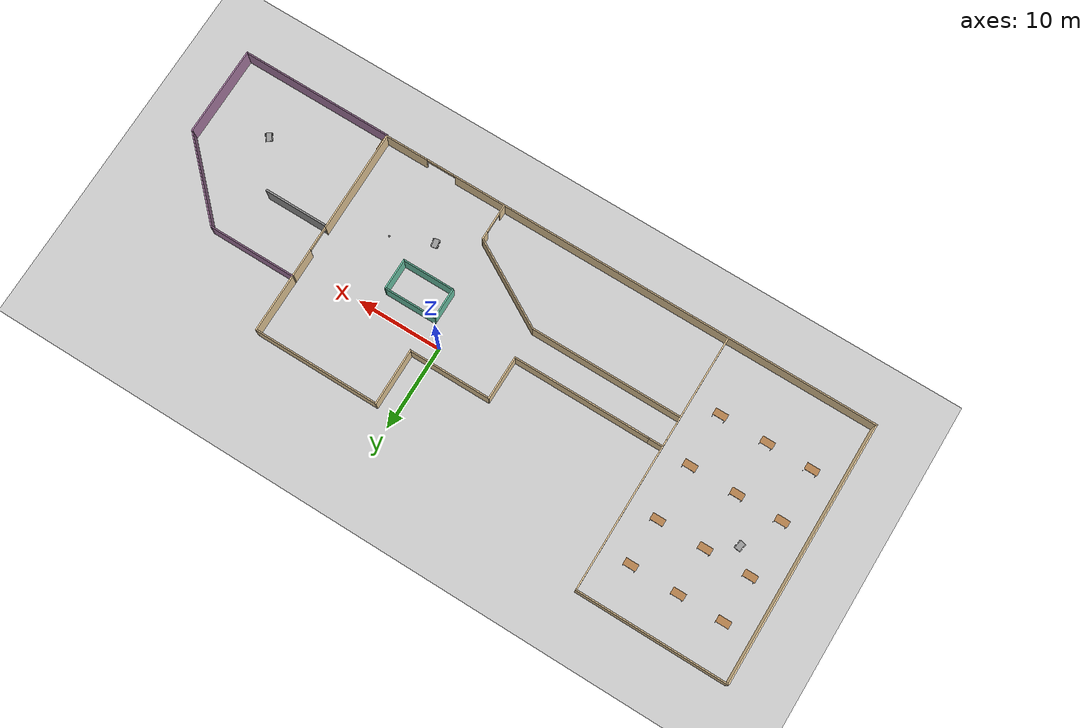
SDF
<sdf version="1.6">
 <world name="default">
  <plugin name="welcome" filename="libwelcome.so"/>
  <light name="sun" type="directional">
   <pose>0 0 10 0 -0 0</pose>
   <diffuse>0.8 0.8 0.8 1</diffuse>
   <specular>0.2 0.2 0.2 1</specular>
   <attenuation>
    <range>1000</range>
    <constant>0.9</constant>
    <linear>0.01</linear>
    <quadratic>0.001</quadratic>
   </attenuation>
   <direction>-0.5 0.1 -0.9</direction>
  </light>
  <model name="ground_plane">
   <static>1</static>
   <link name="link">
    <collision name="collision">
     <geometry><plane><normal>0 0 1</normal><size>100 100</size></plane></geometry>
     <surface>
      <contact><collide_bitmask>65535</collide_bitmask></contact>
      <friction><ode><mu>100</mu><mu2>50</mu2></ode></friction>
     </surface>
    </collision>
    <visual name="visual">
     <cast_shadows>0</cast_shadows>
     <geometry><plane><normal>0 0 1</normal><size>100 100</size></plane></geometry>
     <material>
      <script><uri>file://media/materials/scripts/gazebo.material</uri><name>Gazebo/Grey</name></script>
     </material>
    </visual>
   </link>
  </model>
  <gravity>0 0 -9.8</gravity>
  <magnetic_field>6e-06 2.3e-05 -4.2e-05</magnetic_field>
  <atmosphere type="adiabatic"/>
  <physics name="default_physics" default="0" type="ode">
   <max_step_size>0.001</max_step_size>
   <real_time_factor>1</real_time_factor>
   <real_time_update_rate>1000</real_time_update_rate>
  </physics>
  <scene><ambient>0.4 0.4 0.4 1</ambient><background>0.7 0.7 0.7 1</background><shadows>1</shadows></scene>
  <audio><device>default</device></audio>
  <spherical_coordinates>
   <surface_model>EARTH_WGS84</surface_model>
   <latitude_deg>0</latitude_deg>
   <longitude_deg>0</longitude_deg>
   <elevation>0</elevation>
   <heading_deg>0</heading_deg>
  </spherical_coordinates>
  <model name="office">
   <pose>-3.92011 -1.24039 0 0 -0 0</pose>
   <link name="Wall_0">
    <collision name="Wall_0_Collision">
     <geometry><box><size>5.22347 0.15 2.5</size></box></geometry>
     <pose>0 0 1.25 0 -0 0</pose>
    </collision>
    <visual name="Wall_0_Visual">
     <pose>0 0 1.25 0 -0 0</pose>
     <geometry><box><size>5.22347 0.15 2.5</size></box></geometry>
     <material>
      <script><uri>file://media/materials/scripts/gazebo.material</uri><name>Gazebo/Grey</name></script>
      <ambient>0.921569 0.807843 0.615686 1</ambient>
     </material>
     <meta><layer>0</layer></meta>
    </visual>
    <pose>-3.65319 0.80369 0 0 -0 1.56555</pose>
   </link>
   <link name="Wall_1">
    <collision name="Wall_1_Collision">
     <geometry><box><size>9.75 0.15 2.5</size></box></geometry>
     <pose>0 0 1.25 0 -0 0</pose>
    </collision>
    <visual name="Wall_1_Visual">
     <pose>0 0 1.25 0 -0 0</pose>
     <geometry><box><size>9.75 0.15 2.5</size></box></geometry>
     <material>
      <script><uri>file://media/materials/scripts/gazebo.material</uri><name>Gazebo/Grey</name></script>
      <ambient>0.921569 0.807843 0.615686 1</ambient>
     </material>
     <meta><layer>0</layer></meta>
    </visual>
    <pose>1.16011 3.34039 0 0 -0 0</pose>
   </link>
   <link name="Wall_12">
    <collision name="Wall_12_Collision">
     <geometry><box><size>16.25 0.15 2.5</size></box></geometry>
     <pose>0 0 1.25 0 -0 0</pose>
    </collision>
    <visual name="Wall_12_Visual">
     <pose>0 0 1.25 0 -0 0</pose>
     <geometry><box><size>16.25 0.15 2.5</size></box></geometry>
     <material>
      <script><uri>file://media/materials/scripts/gazebo.material</uri><name>Gazebo/Grey</name></script>
      <ambient>0.921569 0.807843 0.615686 1</ambient>
     </material>
     <meta><layer>0</layer></meta>
    </visual>
    <pose>-11.7165 -1.75961 0 0 -0 3.14159</pose>
   </link>
   <link name="Wall_2">
    <collision name="Wall_2_Collision">
     <geometry><box><size>6.75 0.15 2.5</size></box></geometry>
     <pose>0 0 1.25 0 -0 0</pose>
    </collision>
    <visual name="Wall_2_Visual">
     <pose>0 0 1.25 0 -0 0</pose>
     <geometry><box><size>6.75 0.15 2.5</size></box></geometry>
     <material>
      <script><uri>file://media/materials/scripts/gazebo.material</uri><name>Gazebo/Grey</name></script>
      <ambient>0.921569 0.807843 0.615686 1</ambient>
     </material>
     <meta><layer>0</layer></meta>
    </visual>
    <pose>5.96011 6.64039 0 0 -0 1.5708</pose>
   </link>
   <link name="Wall_25">
    <collision name="Wall_25_Collision">
     <geometry><box><size>18.25 0.15 2.5</size></box></geometry>
     <pose>0 0 1.25 0 -0 0</pose>
    </collision>
    <visual name="Wall_25_Visual">
     <pose>0 0 1.25 0 -0 0</pose>
     <geometry><box><size>18.25 0.15 2.5</size></box></geometry>
     <material>
      <script><uri>file://media/materials/scripts/gazebo.material</uri><name>Gazebo/Grey</name></script>
      <ambient>0.678431 0.498039 0.658824 1</ambient>
     </material>
     <meta><layer>0</layer></meta>
    </visual>
    <pose>29.9204 -15.3405 0 0 -0 0</pose>
   </link>
   <link name="Wall_27">
    <pose>20.8453 -6.08461 0 0 -0 -1.56696</pose>
    <visual name="Wall_27_Visual_0">
     <pose>-7.53879 0 1.25 0 -0 0</pose>
     <geometry><box><size>3.42242 0.15 2.5</size></box></geometry>
     <material>
      <script><uri>file://media/materials/scripts/gazebo.material</uri><name>Gazebo/Grey</name></script>
      <ambient>0.921569 0.807843 0.615686 1</ambient>
     </material>
     <meta><layer>0</layer></meta>
    </visual>
    <collision name="Wall_27_Collision_0">
     <geometry><box><size>3.42242 0.15 2.5</size></box></geometry>
     <pose>-7.53879 0 1.25 0 -0 0</pose>
    </collision>
    <visual name="Wall_27_Visual_1">
     <pose>3.16381 0 1.25 0 -0 0</pose>
     <geometry><box><size>12.1724 0.15 2.5</size></box></geometry>
     <material>
      <script><uri>file://media/materials/scripts/gazebo.material</uri><name>Gazebo/Grey</name></script>
      <ambient>0.921569 0.807843 0.615686 1</ambient>
     </material>
     <meta><layer>0</layer></meta>
    </visual>
    <collision name="Wall_27_Collision_1">
     <geometry><box><size>12.1724 0.15 2.5</size></box></geometry>
     <pose>3.16381 0 1.25 0 -0 0</pose>
    </collision>
    <visual name="Wall_27_Visual_2">
     <pose>-4.37498 0 2.25 0 -0 0</pose>
     <geometry><box><size>2.90519 0.15 0.5</size></box></geometry>
     <material>
      <script><uri>file://media/materials/scripts/gazebo.material</uri><name>Gazebo/Grey</name></script>
      <ambient>0.921569 0.807843 0.615686 1</ambient>
     </material>
     <meta><layer>0</layer></meta>
    </visual>
    <collision name="Wall_27_Collision_2">
     <geometry><box><size>2.90519 0.15 0.5</size></box></geometry>
     <pose>-4.37498 0 2.25 0 -0 0</pose>
    </collision>
   </link>
   <link name="Wall_28">
    <collision name="Wall_28_Collision">
     <geometry><box><size>18 0.15 2.5</size></box></geometry>
     <pose>0 0 1.25 0 -0 0</pose>
    </collision>
    <visual name="Wall_28_Visual">
     <pose>0 0 1.25 0 -0 0</pose>
     <geometry><box><size>18 0.15 2.5</size></box></geometry>
     <material>
      <script><uri>file://media/materials/scripts/gazebo.material</uri><name>Gazebo/Grey</name></script>
      <ambient>0.921569 0.807843 0.615686 1</ambient>
     </material>
     <meta><layer>0</layer></meta>
    </visual>
    <pose>-12.5173 -5.35829 0 0 -0 0</pose>
   </link>
   <link name="Wall_3">
    <collision name="Wall_3_Collision">
     <geometry><box><size>15 0.15 2.5</size></box></geometry>
     <pose>0 0 1.25 0 -0 0</pose>
    </collision>
    <visual name="Wall_3_Visual">
     <pose>0 0 1.25 0 -0 0</pose>
     <geometry><box><size>15 0.15 2.5</size></box></geometry>
     <material>
      <script><uri>file://media/materials/scripts/gazebo.material</uri><name>Gazebo/Grey</name></script>
      <ambient>0.921569 0.807843 0.615686 1</ambient>
     </material>
     <meta><layer>0</layer></meta>
    </visual>
    <pose>13.3851 9.94039 0 0 -0 0</pose>
   </link>
   <link name="Wall_31">
    <pose>-9.07971 -15.2596 0 0 -0 3.14159</pose>
    <visual name="Wall_31_Visual_0">
     <pose>-27.4217 0 1.25 0 -0 0</pose>
     <geometry><box><size>5.15663 0.15 2.5</size></box></geometry>
     <material>
      <script><uri>file://media/materials/scripts/gazebo.material</uri><name>Gazebo/Grey</name></script>
      <ambient>0.921569 0.807843 0.615686 1</ambient>
     </material>
     <meta><layer>0</layer></meta>
    </visual>
    <collision name="Wall_31_Collision_0">
     <geometry><box><size>5.15663 0.15 2.5</size></box></geometry>
     <pose>-27.4217 0 1.25 0 -0 0</pose>
    </collision>
    <visual name="Wall_31_Visual_1">
     <pose>4.35425 0 1.25 0 -0 0</pose>
     <geometry><box><size>51.2915 0.15 2.5</size></box></geometry>
     <material>
      <script><uri>file://media/materials/scripts/gazebo.material</uri><name>Gazebo/Grey</name></script>
      <ambient>0.921569 0.807843 0.615686 1</ambient>
     </material>
     <meta><layer>0</layer></meta>
    </visual>
    <collision name="Wall_31_Collision_1">
     <geometry><box><size>51.2915 0.15 2.5</size></box></geometry>
     <pose>4.35425 0 1.25 0 -0 0</pose>
    </collision>
    <visual name="Wall_31_Visual_2">
     <pose>-23.0674 0 2.25 0 -0 0</pose>
     <geometry><box><size>3.55186 0.15 0.5</size></box></geometry>
     <material>
      <script><uri>file://media/materials/scripts/gazebo.material</uri><name>Gazebo/Grey</name></script>
      <ambient>0.921569 0.807843 0.615686 1</ambient>
     </material>
     <meta><layer>0</layer></meta>
    </visual>
    <collision name="Wall_31_Collision_2">
     <geometry><box><size>3.55186 0.15 0.5</size></box></geometry>
     <pose>-23.0674 0 2.25 0 -0 0</pose>
    </collision>
   </link>
   <link name="Wall_32">
    <collision name="Wall_32_Collision">
     <geometry><box><size>30.75 0.15 2.5</size></box></geometry>
     <pose>0 0 1.25 0 -0 0</pose>
    </collision>
    <visual name="Wall_32_Visual">
     <pose>0 0 1.25 0 -0 0</pose>
     <geometry><box><size>30.75 0.15 2.5</size></box></geometry>
     <material>
      <script><uri>file://media/materials/scripts/gazebo.material</uri><name>Gazebo/Grey</name></script>
      <ambient>0.921569 0.807843 0.615686 1</ambient>
     </material>
     <meta><layer>0</layer></meta>
    </visual>
    <pose>-39.0047 0.04039 0 0 -0 1.5731</pose>
   </link>
   <link name="Wall_33">
    <collision name="Wall_33_Collision">
     <geometry><box><size>17.75 0.15 2.5</size></box></geometry>
     <pose>0 0 1.25 0 -0 0</pose>
    </collision>
    <visual name="Wall_33_Visual">
     <pose>0 0 1.25 0 -0 0</pose>
     <geometry><box><size>17.75 0.15 2.5</size></box></geometry>
     <material>
      <script><uri>file://media/materials/scripts/gazebo.material</uri><name>Gazebo/Grey</name></script>
      <ambient>0.921569 0.807843 0.615686 1</ambient>
     </material>
     <meta><layer>0</layer></meta>
    </visual>
    <pose>-30.2399 15.3404 0 0 -0 0</pose>
   </link>
   <link name="Wall_34">
    <pose>-21.4399 0.04039 0 0 -0 -1.5708</pose>
    <visual name="Wall_34_Visual_0">
     <pose>-6.3674 0 1.25 0 -0 0</pose>
     <geometry><box><size>18.0152 0.15 2.5</size></box></geometry>
     <material>
      <script><uri>file://media/materials/scripts/gazebo.material</uri><name>Gazebo/Grey</name></script>
      <ambient>0.921569 0.807843 0.615686 1</ambient>
     </material>
     <meta><layer>0</layer></meta>
    </visual>
    <collision name="Wall_34_Collision_0">
     <geometry><box><size>18.0152 0.15 2.5</size></box></geometry>
     <pose>-6.3674 0 1.25 0 -0 0</pose>
    </collision>
    <visual name="Wall_34_Visual_1">
     <pose>10.1 0 1.25 0 -0 0</pose>
     <geometry><box><size>10.55 0.15 2.5</size></box></geometry>
     <material>
      <script><uri>file://media/materials/scripts/gazebo.material</uri><name>Gazebo/Grey</name></script>
      <ambient>0.921569 0.807843 0.615686 1</ambient>
     </material>
     <meta><layer>0</layer></meta>
    </visual>
    <collision name="Wall_34_Collision_1">
     <geometry><box><size>10.55 0.15 2.5</size></box></geometry>
     <pose>10.1 0 1.25 0 -0 0</pose>
    </collision>
    <visual name="Wall_34_Visual_2">
     <pose>3.7326 0 2.25 0 -0 0</pose>
     <geometry><box><size>2.18479 0.15 0.5</size></box></geometry>
     <material>
      <script><uri>file://media/materials/scripts/gazebo.material</uri><name>Gazebo/Grey</name></script>
      <ambient>0.921569 0.807843 0.615686 1</ambient>
     </material>
     <meta><layer>0</layer></meta>
    </visual>
    <collision name="Wall_34_Collision_2">
     <geometry><box><size>2.18479 0.15 0.5</size></box></geometry>
     <pose>3.7326 0 2.25 0 -0 0</pose>
    </collision>
   </link>
   <link name="Wall_36">
    <collision name="Wall_36_Collision">
     <geometry><box><size>1.75 0.15 2.5</size></box></geometry>
     <pose>0 0 1.25 0 -0 0</pose>
    </collision>
    <visual name="Wall_36_Visual">
     <pose>0 0 1.25 0 -0 0</pose>
     <geometry><box><size>1.75 0.15 2.5</size></box></geometry>
     <material>
      <script><uri>file://media/materials/scripts/gazebo.material</uri><name>Gazebo/Grey</name></script>
      <ambient>0.921569 0.807843 0.615686 1</ambient>
     </material>
     <meta><layer>0</layer></meta>
    </visual>
    <pose>-20.5665 -1.75961 0 0 -0 3.14159</pose>
   </link>
   <link name="Wall_38">
    <collision name="Wall_38_Collision">
     <geometry><box><size>11.25 0.15 2.5</size></box></geometry>
     <pose>0 0 1.25 0 -0 0</pose>
    </collision>
    <visual name="Wall_38_Visual">
     <pose>0 0 1.25 0 -0 0</pose>
     <geometry><box><size>11.25 0.15 2.5</size></box></geometry>
     <material>
      <script><uri>file://media/materials/scripts/gazebo.material</uri><name>Gazebo/Grey</name></script>
      <ambient>0.921569 0.807843 0.615686 1</ambient>
     </material>
     <meta><layer>0</layer></meta>
    </visual>
    <pose>1.21412 -8.13329 0 0 -0 -0.523599</pose>
   </link>
   <link name="Wall_39">
    <pose>6.02056 -13.0833 0 0 -0 -1.5708</pose>
    <visual name="Wall_39_Visual_0">
     <pose>-1.78066 0 1.25 0 -0 0</pose>
     <geometry><box><size>0.938674 0.15 2.5</size></box></geometry>
     <material>
      <script><uri>file://media/materials/scripts/gazebo.material</uri><name>Gazebo/Grey</name></script>
      <ambient>0.921569 0.807843 0.615686 1</ambient>
     </material>
     <meta><layer>0</layer></meta>
    </visual>
    <collision name="Wall_39_Collision_0">
     <geometry><box><size>0.938674 0.15 2.5</size></box></geometry>
     <pose>-1.78066 0 1.25 0 -0 0</pose>
    </collision>
    <visual name="Wall_39_Visual_1">
     <pose>1.71425 0 1.25 0 -0 0</pose>
     <geometry><box><size>1.07151 0.15 2.5</size></box></geometry>
     <material>
      <script><uri>file://media/materials/scripts/gazebo.material</uri><name>Gazebo/Grey</name></script>
      <ambient>0.921569 0.807843 0.615686 1</ambient>
     </material>
     <meta><layer>0</layer></meta>
    </visual>
    <collision name="Wall_39_Collision_1">
     <geometry><box><size>1.07151 0.15 2.5</size></box></geometry>
     <pose>1.71425 0 1.25 0 -0 0</pose>
    </collision>
    <visual name="Wall_39_Visual_2">
     <pose>-0.066418 0 2.25 0 -0 0</pose>
     <geometry><box><size>2.48982 0.15 0.5</size></box></geometry>
     <material>
      <script><uri>file://media/materials/scripts/gazebo.material</uri><name>Gazebo/Grey</name></script>
      <ambient>0.921569 0.807843 0.615686 1</ambient>
     </material>
     <meta><layer>0</layer></meta>
    </visual>
    <collision name="Wall_39_Collision_2">
     <geometry><box><size>2.48982 0.15 0.5</size></box></geometry>
     <pose>-0.066418 0 2.25 0 -0 0</pose>
    </collision>
   </link>
   <link name="Wall_41">
    <collision name="Wall_41_Collision">
     <geometry><box><size>3.75 0.15 2.5</size></box></geometry>
     <pose>0 0 1.25 0 -0 0</pose>
    </collision>
    <visual name="Wall_41_Visual">
     <pose>0 0 1.25 0 -0 0</pose>
     <geometry><box><size>3.75 0.15 2.5</size></box></geometry>
     <material>
      <script><uri>file://media/materials/scripts/gazebo.material</uri><name>Gazebo/Grey</name></script>
      <ambient>0.435294 0.796078 0.67451 1</ambient>
     </material>
     <meta><layer>0</layer></meta>
    </visual>
    <pose>5.72064 -2.74195 0 0 -0 -1.5708</pose>
   </link>
   <link name="Wall_42">
    <collision name="Wall_42_Collision">
     <geometry><box><size>6.25 0.15 2.5</size></box></geometry>
     <pose>0 0 1.25 0 -0 0</pose>
    </collision>
    <visual name="Wall_42_Visual">
     <pose>0 0 1.25 0 -0 0</pose>
     <geometry><box><size>6.25 0.15 2.5</size></box></geometry>
     <material>
      <script><uri>file://media/materials/scripts/gazebo.material</uri><name>Gazebo/Grey</name></script>
      <ambient>0.435294 0.796078 0.67451 1</ambient>
     </material>
     <meta><layer>0</layer></meta>
    </visual>
    <pose>8.77064 -4.54195 0 0 -0 0</pose>
   </link>
   <link name="Wall_43">
    <collision name="Wall_43_Collision">
     <geometry><box><size>3.75 0.15 2.5</size></box></geometry>
     <pose>0 0 1.25 0 -0 0</pose>
    </collision>
    <visual name="Wall_43_Visual">
     <pose>0 0 1.25 0 -0 0</pose>
     <geometry><box><size>3.75 0.15 2.5</size></box></geometry>
     <material>
      <script><uri>file://media/materials/scripts/gazebo.material</uri><name>Gazebo/Grey</name></script>
      <ambient>0.435294 0.796078 0.67451 1</ambient>
     </material>
     <meta><layer>0</layer></meta>
    </visual>
    <pose>11.8206 -2.74195 0 0 -0 1.5708</pose>
   </link>
   <link name="Wall_44">
    <collision name="Wall_44_Collision">
     <geometry><box><size>6.25 0.15 2.5</size></box></geometry>
     <pose>0 0 1.25 0 -0 0</pose>
    </collision>
    <visual name="Wall_44_Visual">
     <pose>0 0 1.25 0 -0 0</pose>
     <geometry><box><size>6.25 0.15 2.5</size></box></geometry>
     <material>
      <script><uri>file://media/materials/scripts/gazebo.material</uri><name>Gazebo/Grey</name></script>
      <ambient>0.435294 0.796078 0.67451 1</ambient>
     </material>
     <meta><layer>0</layer></meta>
    </visual>
    <pose>8.77064 -0.941952 0 0 -0 3.14159</pose>
   </link>
   <link name="Wall_6">
    <collision name="Wall_6_Collision">
     <geometry><box><size>7 0.15 2.5</size></box></geometry>
     <pose>0 0 1.25 0 -0 0</pose>
    </collision>
    <visual name="Wall_6_Visual">
     <pose>0 0 1.25 0 -0 0</pose>
     <geometry><box><size>7 0.15 2.5</size></box></geometry>
     <material>
      <script><uri>file://media/materials/scripts/gazebo.material</uri><name>Gazebo/Grey</name></script>
      <ambient>0.921569 0.807843 0.615686 1</ambient>
     </material>
     <meta><layer>0</layer></meta>
    </visual>
    <pose>20.8101 6.51539 0 0 -0 -1.5708</pose>
   </link>
   <link name="Wall_7">
    <collision name="Wall_7_Collision">
     <geometry><box><size>10.5 0.15 2.5</size></box></geometry>
     <pose>0 0 1.25 0 -0 0</pose>
    </collision>
    <visual name="Wall_7_Visual">
     <pose>0 0 1.25 0 -0 0</pose>
     <geometry><box><size>10.5 0.15 2.5</size></box></geometry>
     <material>
      <script><uri>file://media/materials/scripts/gazebo.material</uri><name>Gazebo/Grey</name></script>
      <ambient>0.678431 0.498039 0.658824 1</ambient>
     </material>
     <meta><layer>0</layer></meta>
    </visual>
    <pose>25.9851 3.09039 0 0 -0 0</pose>
   </link>
   <link name="Wall_8">
    <collision name="Wall_8_Collision">
     <geometry><box><size>11.25 0.15 2.5</size></box></geometry>
     <pose>0 0 1.25 0 -0 0</pose>
    </collision>
    <visual name="Wall_8_Visual">
     <pose>0 0 1.25 0 -0 0</pose>
     <geometry><box><size>11.25 0.15 2.5</size></box></geometry>
     <material>
      <script><uri>file://media/materials/scripts/gazebo.material</uri><name>Gazebo/Grey</name></script>
      <ambient>0.678431 0.498039 0.658824 1</ambient>
     </material>
     <meta><layer>0</layer></meta>
    </visual>
    <pose>35.0846 -0.834053 0 0 -0 -0.785398</pose>
   </link>
   <link name="Wall_9">
    <collision name="Wall_9_Collision">
     <geometry><box><size>10.7102 0.15 2.5</size></box></geometry>
     <pose>0 0 1.25 0 -0 0</pose>
    </collision>
    <visual name="Wall_9_Visual">
     <pose>0 0 1.25 0 -0 0</pose>
     <geometry><box><size>10.7102 0.15 2.5</size></box></geometry>
     <material>
      <script><uri>file://media/materials/scripts/gazebo.material</uri><name>Gazebo/Grey</name></script>
      <ambient>0.678431 0.498039 0.658824 1</ambient>
     </material>
     <meta><layer>0</layer></meta>
    </visual>
    <pose>39.009 -10.0383 0 0 -0 -1.5708</pose>
   </link>
   <static>1</static>
  </model>
  <model name="table">
   <static>1</static>
   <link name="link">
    <collision name="surface">
     <pose>0 0 1 0 -0 0</pose>
     <geometry><box><size>1.5 0.8 0.03</size></box></geometry>
     <surface><friction><ode><mu>0.6</mu><mu2>0.6</mu2></ode></friction></surface>
    </collision>
    <visual name="visual1">
     <pose>0 0 1 0 -0 0</pose>
     <geometry><box><size>1.5 0.8 0.03</size></box></geometry>
     <material>
      <script><uri>file://media/materials/scripts/gazebo.material</uri><name>Gazebo/Wood</name></script>
     </material>
    </visual>
    <collision name="front_left_leg">
     <pose>0.68 0.38 0.5 0 -0 0</pose>
     <geometry><cylinder><radius>0.02</radius><length>1</length></cylinder></geometry>
    </collision>
    <visual name="front_left_leg">
     <pose>0.68 0.38 0.5 0 -0 0</pose>
     <geometry><cylinder><radius>0.02</radius><length>1</length></cylinder></geometry>
     <material>
      <script><uri>file://media/materials/scripts/gazebo.material</uri><name>Gazebo/Grey</name></script>
     </material>
    </visual>
    <collision name="front_right_leg">
     <pose>0.68 -0.38 0.5 0 -0 0</pose>
     <geometry><cylinder><radius>0.02</radius><length>1</length></cylinder></geometry>
    </collision>
    <visual name="front_right_leg">
     <pose>0.68 -0.38 0.5 0 -0 0</pose>
     <geometry><cylinder><radius>0.02</radius><length>1</length></cylinder></geometry>
     <material>
      <script><uri>file://media/materials/scripts/gazebo.material</uri><name>Gazebo/Grey</name></script>
     </material>
    </visual>
    <collision name="back_right_leg">
     <pose>-0.68 -0.38 0.5 0 -0 0</pose>
     <geometry><cylinder><radius>0.02</radius><length>1</length></cylinder></geometry>
    </collision>
    <visual name="back_right_leg">
     <pose>-0.68 -0.38 0.5 0 -0 0</pose>
     <geometry><cylinder><radius>0.02</radius><length>1</length></cylinder></geometry>
     <material>
      <script><uri>file://media/materials/scripts/gazebo.material</uri><name>Gazebo/Grey</name></script>
     </material>
    </visual>
    <collision name="back_left_leg">
     <pose>-0.68 0.38 0.5 0 -0 0</pose>
     <geometry><cylinder><radius>0.02</radius><length>1</length></cylinder></geometry>
    </collision>
    <visual name="back_left_leg">
     <pose>-0.68 0.38 0.5 0 -0 0</pose>
     <geometry><cylinder><radius>0.02</radius><length>1</length></cylinder></geometry>
     <material>
      <script><uri>file://media/materials/scripts/gazebo.material</uri><name>Gazebo/Grey</name></script>
     </material>
    </visual>
   </link>
   <pose>-39.638 8.8822 0 0 -0 0</pose>
  </model>
  <model name="table_clone">
   <static>1</static>
   <link name="link">
    <collision name="surface">
     <pose>0 0 1 0 -0 0</pose>
     <geometry><box><size>1.5 0.8 0.03</size></box></geometry>
     <surface><friction><ode><mu>0.6</mu><mu2>0.6</mu2></ode></friction></surface>
    </collision>
    <visual name="visual1">
     <pose>0 0 1 0 -0 0</pose>
     <geometry><box><size>1.5 0.8 0.03</size></box></geometry>
     <material>
      <script><uri>file://media/materials/scripts/gazebo.material</uri><name>Gazebo/Wood</name></script>
     </material>
    </visual>
    <collision name="front_left_leg">
     <pose>0.68 0.38 0.5 0 -0 0</pose>
     <geometry><cylinder><radius>0.02</radius><length>1</length></cylinder></geometry>
    </collision>
    <visual name="front_left_leg">
     <pose>0.68 0.38 0.5 0 -0 0</pose>
     <geometry><cylinder><radius>0.02</radius><length>1</length></cylinder></geometry>
     <material>
      <script><uri>file://media/materials/scripts/gazebo.material</uri><name>Gazebo/Grey</name></script>
     </material>
    </visual>
    <collision name="front_right_leg">
     <pose>0.68 -0.38 0.5 0 -0 0</pose>
     <geometry><cylinder><radius>0.02</radius><length>1</length></cylinder></geometry>
    </collision>
    <visual name="front_right_leg">
     <pose>0.68 -0.38 0.5 0 -0 0</pose>
     <geometry><cylinder><radius>0.02</radius><length>1</length></cylinder></geometry>
     <material>
      <script><uri>file://media/materials/scripts/gazebo.material</uri><name>Gazebo/Grey</name></script>
     </material>
    </visual>
    <collision name="back_right_leg">
     <pose>-0.68 -0.38 0.5 0 -0 0</pose>
     <geometry><cylinder><radius>0.02</radius><length>1</length></cylinder></geometry>
    </collision>
    <visual name="back_right_leg">
     <pose>-0.68 -0.38 0.5 0 -0 0</pose>
     <geometry><cylinder><radius>0.02</radius><length>1</length></cylinder></geometry>
     <material>
      <script><uri>file://media/materials/scripts/gazebo.material</uri><name>Gazebo/Grey</name></script>
     </material>
    </visual>
    <collision name="back_left_leg">
     <pose>-0.68 0.38 0.5 0 -0 0</pose>
     <geometry><cylinder><radius>0.02</radius><length>1</length></cylinder></geometry>
    </collision>
    <visual name="back_left_leg">
     <pose>-0.68 0.38 0.5 0 -0 0</pose>
     <geometry><cylinder><radius>0.02</radius><length>1</length></cylinder></geometry>
     <material>
      <script><uri>file://media/materials/scripts/gazebo.material</uri><name>Gazebo/Grey</name></script>
     </material>
    </visual>
   </link>
   <pose>-34.3535 8.8822 0 0 -0 0</pose>
  </model>
  <model name="table_clone_1">
   <static>1</static>
   <link name="link">
    <collision name="surface">
     <pose>0 0 1 0 -0 0</pose>
     <geometry><box><size>1.5 0.8 0.03</size></box></geometry>
     <surface><friction><ode><mu>0.6</mu><mu2>0.6</mu2></ode></friction></surface>
    </collision>
    <visual name="visual1">
     <pose>0 0 1 0 -0 0</pose>
     <geometry><box><size>1.5 0.8 0.03</size></box></geometry>
     <material>
      <script><uri>file://media/materials/scripts/gazebo.material</uri><name>Gazebo/Wood</name></script>
     </material>
    </visual>
    <collision name="front_left_leg">
     <pose>0.68 0.38 0.5 0 -0 0</pose>
     <geometry><cylinder><radius>0.02</radius><length>1</length></cylinder></geometry>
    </collision>
    <visual name="front_left_leg">
     <pose>0.68 0.38 0.5 0 -0 0</pose>
     <geometry><cylinder><radius>0.02</radius><length>1</length></cylinder></geometry>
     <material>
      <script><uri>file://media/materials/scripts/gazebo.material</uri><name>Gazebo/Grey</name></script>
     </material>
    </visual>
    <collision name="front_right_leg">
     <pose>0.68 -0.38 0.5 0 -0 0</pose>
     <geometry><cylinder><radius>0.02</radius><length>1</length></cylinder></geometry>
    </collision>
    <visual name="front_right_leg">
     <pose>0.68 -0.38 0.5 0 -0 0</pose>
     <geometry><cylinder><radius>0.02</radius><length>1</length></cylinder></geometry>
     <material>
      <script><uri>file://media/materials/scripts/gazebo.material</uri><name>Gazebo/Grey</name></script>
     </material>
    </visual>
    <collision name="back_right_leg">
     <pose>-0.68 -0.38 0.5 0 -0 0</pose>
     <geometry><cylinder><radius>0.02</radius><length>1</length></cylinder></geometry>
    </collision>
    <visual name="back_right_leg">
     <pose>-0.68 -0.38 0.5 0 -0 0</pose>
     <geometry><cylinder><radius>0.02</radius><length>1</length></cylinder></geometry>
     <material>
      <script><uri>file://media/materials/scripts/gazebo.material</uri><name>Gazebo/Grey</name></script>
     </material>
    </visual>
    <collision name="back_left_leg">
     <pose>-0.68 0.38 0.5 0 -0 0</pose>
     <geometry><cylinder><radius>0.02</radius><length>1</length></cylinder></geometry>
    </collision>
    <visual name="back_left_leg">
     <pose>-0.68 0.38 0.5 0 -0 0</pose>
     <geometry><cylinder><radius>0.02</radius><length>1</length></cylinder></geometry>
     <material>
      <script><uri>file://media/materials/scripts/gazebo.material</uri><name>Gazebo/Grey</name></script>
     </material>
    </visual>
   </link>
   <pose>-39.638 3.48413 0 0 -0 0</pose>
  </model>
  <model name="table_clone_3">
   <static>1</static>
   <link name="link">
    <collision name="surface">
     <pose>0 0 1 0 -0 0</pose>
     <geometry><box><size>1.5 0.8 0.03</size></box></geometry>
     <surface><friction><ode><mu>0.6</mu><mu2>0.6</mu2></ode></friction></surface>
    </collision>
    <visual name="visual1">
     <pose>0 0 1 0 -0 0</pose>
     <geometry><box><size>1.5 0.8 0.03</size></box></geometry>
     <material>
      <script><uri>file://media/materials/scripts/gazebo.material</uri><name>Gazebo/Wood</name></script>
     </material>
    </visual>
    <collision name="front_left_leg">
     <pose>0.68 0.38 0.5 0 -0 0</pose>
     <geometry><cylinder><radius>0.02</radius><length>1</length></cylinder></geometry>
    </collision>
    <visual name="front_left_leg">
     <pose>0.68 0.38 0.5 0 -0 0</pose>
     <geometry><cylinder><radius>0.02</radius><length>1</length></cylinder></geometry>
     <material>
      <script><uri>file://media/materials/scripts/gazebo.material</uri><name>Gazebo/Grey</name></script>
     </material>
    </visual>
    <collision name="front_right_leg">
     <pose>0.68 -0.38 0.5 0 -0 0</pose>
     <geometry><cylinder><radius>0.02</radius><length>1</length></cylinder></geometry>
    </collision>
    <visual name="front_right_leg">
     <pose>0.68 -0.38 0.5 0 -0 0</pose>
     <geometry><cylinder><radius>0.02</radius><length>1</length></cylinder></geometry>
     <material>
      <script><uri>file://media/materials/scripts/gazebo.material</uri><name>Gazebo/Grey</name></script>
     </material>
    </visual>
    <collision name="back_right_leg">
     <pose>-0.68 -0.38 0.5 0 -0 0</pose>
     <geometry><cylinder><radius>0.02</radius><length>1</length></cylinder></geometry>
    </collision>
    <visual name="back_right_leg">
     <pose>-0.68 -0.38 0.5 0 -0 0</pose>
     <geometry><cylinder><radius>0.02</radius><length>1</length></cylinder></geometry>
     <material>
      <script><uri>file://media/materials/scripts/gazebo.material</uri><name>Gazebo/Grey</name></script>
     </material>
    </visual>
    <collision name="back_left_leg">
     <pose>-0.68 0.38 0.5 0 -0 0</pose>
     <geometry><cylinder><radius>0.02</radius><length>1</length></cylinder></geometry>
    </collision>
    <visual name="back_left_leg">
     <pose>-0.68 0.38 0.5 0 -0 0</pose>
     <geometry><cylinder><radius>0.02</radius><length>1</length></cylinder></geometry>
     <material>
      <script><uri>file://media/materials/scripts/gazebo.material</uri><name>Gazebo/Grey</name></script>
     </material>
    </visual>
   </link>
   <pose>-28.7648 3.48413 0 0 -0 0</pose>
  </model>
  <model name="table_clone_clone">
   <static>1</static>
   <link name="link">
    <collision name="surface">
     <pose>0 0 1 0 -0 0</pose>
     <geometry><box><size>1.5 0.8 0.03</size></box></geometry>
     <surface><friction><ode><mu>0.6</mu><mu2>0.6</mu2></ode></friction></surface>
    </collision>
    <visual name="visual1">
     <pose>0 0 1 0 -0 0</pose>
     <geometry><box><size>1.5 0.8 0.03</size></box></geometry>
     <material>
      <script><uri>file://media/materials/scripts/gazebo.material</uri><name>Gazebo/Wood</name></script>
     </material>
    </visual>
    <collision name="front_left_leg">
     <pose>0.68 0.38 0.5 0 -0 0</pose>
     <geometry><cylinder><radius>0.02</radius><length>1</length></cylinder></geometry>
    </collision>
    <visual name="front_left_leg">
     <pose>0.68 0.38 0.5 0 -0 0</pose>
     <geometry><cylinder><radius>0.02</radius><length>1</length></cylinder></geometry>
     <material>
      <script><uri>file://media/materials/scripts/gazebo.material</uri><name>Gazebo/Grey</name></script>
     </material>
    </visual>
    <collision name="front_right_leg">
     <pose>0.68 -0.38 0.5 0 -0 0</pose>
     <geometry><cylinder><radius>0.02</radius><length>1</length></cylinder></geometry>
    </collision>
    <visual name="front_right_leg">
     <pose>0.68 -0.38 0.5 0 -0 0</pose>
     <geometry><cylinder><radius>0.02</radius><length>1</length></cylinder></geometry>
     <material>
      <script><uri>file://media/materials/scripts/gazebo.material</uri><name>Gazebo/Grey</name></script>
     </material>
    </visual>
    <collision name="back_right_leg">
     <pose>-0.68 -0.38 0.5 0 -0 0</pose>
     <geometry><cylinder><radius>0.02</radius><length>1</length></cylinder></geometry>
    </collision>
    <visual name="back_right_leg">
     <pose>-0.68 -0.38 0.5 0 -0 0</pose>
     <geometry><cylinder><radius>0.02</radius><length>1</length></cylinder></geometry>
     <material>
      <script><uri>file://media/materials/scripts/gazebo.material</uri><name>Gazebo/Grey</name></script>
     </material>
    </visual>
    <collision name="back_left_leg">
     <pose>-0.68 0.38 0.5 0 -0 0</pose>
     <geometry><cylinder><radius>0.02</radius><length>1</length></cylinder></geometry>
    </collision>
    <visual name="back_left_leg">
     <pose>-0.68 0.38 0.5 0 -0 0</pose>
     <geometry><cylinder><radius>0.02</radius><length>1</length></cylinder></geometry>
     <material>
      <script><uri>file://media/materials/scripts/gazebo.material</uri><name>Gazebo/Grey</name></script>
     </material>
    </visual>
   </link>
   <pose>-28.7648 8.8822 0 0 -0 0</pose>
  </model>
  <model name="table_clone_0">
   <static>1</static>
   <link name="link">
    <collision name="surface">
     <pose>0 0 1 0 -0 0</pose>
     <geometry><box><size>1.5 0.8 0.03</size></box></geometry>
     <surface><friction><ode><mu>0.6</mu><mu2>0.6</mu2></ode></friction></surface>
    </collision>
    <visual name="visual1">
     <pose>0 0 1 0 -0 0</pose>
     <geometry><box><size>1.5 0.8 0.03</size></box></geometry>
     <material>
      <script><uri>file://media/materials/scripts/gazebo.material</uri><name>Gazebo/Wood</name></script>
     </material>
    </visual>
    <collision name="front_left_leg">
     <pose>0.68 0.38 0.5 0 -0 0</pose>
     <geometry><cylinder><radius>0.02</radius><length>1</length></cylinder></geometry>
    </collision>
    <visual name="front_left_leg">
     <pose>0.68 0.38 0.5 0 -0 0</pose>
     <geometry><cylinder><radius>0.02</radius><length>1</length></cylinder></geometry>
     <material>
      <script><uri>file://media/materials/scripts/gazebo.material</uri><name>Gazebo/Grey</name></script>
     </material>
    </visual>
    <collision name="front_right_leg">
     <pose>0.68 -0.38 0.5 0 -0 0</pose>
     <geometry><cylinder><radius>0.02</radius><length>1</length></cylinder></geometry>
    </collision>
    <visual name="front_right_leg">
     <pose>0.68 -0.38 0.5 0 -0 0</pose>
     <geometry><cylinder><radius>0.02</radius><length>1</length></cylinder></geometry>
     <material>
      <script><uri>file://media/materials/scripts/gazebo.material</uri><name>Gazebo/Grey</name></script>
     </material>
    </visual>
    <collision name="back_right_leg">
     <pose>-0.68 -0.38 0.5 0 -0 0</pose>
     <geometry><cylinder><radius>0.02</radius><length>1</length></cylinder></geometry>
    </collision>
    <visual name="back_right_leg">
     <pose>-0.68 -0.38 0.5 0 -0 0</pose>
     <geometry><cylinder><radius>0.02</radius><length>1</length></cylinder></geometry>
     <material>
      <script><uri>file://media/materials/scripts/gazebo.material</uri><name>Gazebo/Grey</name></script>
     </material>
    </visual>
    <collision name="back_left_leg">
     <pose>-0.68 0.38 0.5 0 -0 0</pose>
     <geometry><cylinder><radius>0.02</radius><length>1</length></cylinder></geometry>
    </collision>
    <visual name="back_left_leg">
     <pose>-0.68 0.38 0.5 0 -0 0</pose>
     <geometry><cylinder><radius>0.02</radius><length>1</length></cylinder></geometry>
     <material>
      <script><uri>file://media/materials/scripts/gazebo.material</uri><name>Gazebo/Grey</name></script>
     </material>
    </visual>
   </link>
   <pose>-34.3535 3.48413 0 0 -0 0</pose>
  </model>
  <model name="table_clone_1_clone">
   <static>1</static>
   <link name="link">
    <collision name="surface">
     <pose>0 0 1 0 -0 0</pose>
     <geometry><box><size>1.5 0.8 0.03</size></box></geometry>
     <surface><friction><ode><mu>0.6</mu><mu2>0.6</mu2></ode></friction></surface>
    </collision>
    <visual name="visual1">
     <pose>0 0 1 0 -0 0</pose>
     <geometry><box><size>1.5 0.8 0.03</size></box></geometry>
     <material>
      <script><uri>file://media/materials/scripts/gazebo.material</uri><name>Gazebo/Wood</name></script>
     </material>
    </visual>
    <collision name="front_left_leg">
     <pose>0.68 0.38 0.5 0 -0 0</pose>
     <geometry><cylinder><radius>0.02</radius><length>1</length></cylinder></geometry>
    </collision>
    <visual name="front_left_leg">
     <pose>0.68 0.38 0.5 0 -0 0</pose>
     <geometry><cylinder><radius>0.02</radius><length>1</length></cylinder></geometry>
     <material>
      <script><uri>file://media/materials/scripts/gazebo.material</uri><name>Gazebo/Grey</name></script>
     </material>
    </visual>
    <collision name="front_right_leg">
     <pose>0.68 -0.38 0.5 0 -0 0</pose>
     <geometry><cylinder><radius>0.02</radius><length>1</length></cylinder></geometry>
    </collision>
    <visual name="front_right_leg">
     <pose>0.68 -0.38 0.5 0 -0 0</pose>
     <geometry><cylinder><radius>0.02</radius><length>1</length></cylinder></geometry>
     <material>
      <script><uri>file://media/materials/scripts/gazebo.material</uri><name>Gazebo/Grey</name></script>
     </material>
    </visual>
    <collision name="back_right_leg">
     <pose>-0.68 -0.38 0.5 0 -0 0</pose>
     <geometry><cylinder><radius>0.02</radius><length>1</length></cylinder></geometry>
    </collision>
    <visual name="back_right_leg">
     <pose>-0.68 -0.38 0.5 0 -0 0</pose>
     <geometry><cylinder><radius>0.02</radius><length>1</length></cylinder></geometry>
     <material>
      <script><uri>file://media/materials/scripts/gazebo.material</uri><name>Gazebo/Grey</name></script>
     </material>
    </visual>
    <collision name="back_left_leg">
     <pose>-0.68 0.38 0.5 0 -0 0</pose>
     <geometry><cylinder><radius>0.02</radius><length>1</length></cylinder></geometry>
    </collision>
    <visual name="back_left_leg">
     <pose>-0.68 0.38 0.5 0 -0 0</pose>
     <geometry><cylinder><radius>0.02</radius><length>1</length></cylinder></geometry>
     <material>
      <script><uri>file://media/materials/scripts/gazebo.material</uri><name>Gazebo/Grey</name></script>
     </material>
    </visual>
   </link>
   <pose>-39.638 -3.0757 0 0 -0 0</pose>
  </model>
  <model name="table_clone_1_clone_0">
   <static>1</static>
   <link name="link">
    <collision name="surface">
     <pose>0 0 1 0 -0 0</pose>
     <geometry><box><size>1.5 0.8 0.03</size></box></geometry>
     <surface><friction><ode><mu>0.6</mu><mu2>0.6</mu2></ode></friction></surface>
    </collision>
    <visual name="visual1">
     <pose>0 0 1 0 -0 0</pose>
     <geometry><box><size>1.5 0.8 0.03</size></box></geometry>
     <material>
      <script><uri>file://media/materials/scripts/gazebo.material</uri><name>Gazebo/Wood</name></script>
     </material>
    </visual>
    <collision name="front_left_leg">
     <pose>0.68 0.38 0.5 0 -0 0</pose>
     <geometry><cylinder><radius>0.02</radius><length>1</length></cylinder></geometry>
    </collision>
    <visual name="front_left_leg">
     <pose>0.68 0.38 0.5 0 -0 0</pose>
     <geometry><cylinder><radius>0.02</radius><length>1</length></cylinder></geometry>
     <material>
      <script><uri>file://media/materials/scripts/gazebo.material</uri><name>Gazebo/Grey</name></script>
     </material>
    </visual>
    <collision name="front_right_leg">
     <pose>0.68 -0.38 0.5 0 -0 0</pose>
     <geometry><cylinder><radius>0.02</radius><length>1</length></cylinder></geometry>
    </collision>
    <visual name="front_right_leg">
     <pose>0.68 -0.38 0.5 0 -0 0</pose>
     <geometry><cylinder><radius>0.02</radius><length>1</length></cylinder></geometry>
     <material>
      <script><uri>file://media/materials/scripts/gazebo.material</uri><name>Gazebo/Grey</name></script>
     </material>
    </visual>
    <collision name="back_right_leg">
     <pose>-0.68 -0.38 0.5 0 -0 0</pose>
     <geometry><cylinder><radius>0.02</radius><length>1</length></cylinder></geometry>
    </collision>
    <visual name="back_right_leg">
     <pose>-0.68 -0.38 0.5 0 -0 0</pose>
     <geometry><cylinder><radius>0.02</radius><length>1</length></cylinder></geometry>
     <material>
      <script><uri>file://media/materials/scripts/gazebo.material</uri><name>Gazebo/Grey</name></script>
     </material>
    </visual>
    <collision name="back_left_leg">
     <pose>-0.68 0.38 0.5 0 -0 0</pose>
     <geometry><cylinder><radius>0.02</radius><length>1</length></cylinder></geometry>
    </collision>
    <visual name="back_left_leg">
     <pose>-0.68 0.38 0.5 0 -0 0</pose>
     <geometry><cylinder><radius>0.02</radius><length>1</length></cylinder></geometry>
     <material>
      <script><uri>file://media/materials/scripts/gazebo.material</uri><name>Gazebo/Grey</name></script>
     </material>
    </visual>
   </link>
   <pose>-34.3535 -3.0757 0 0 -0 0</pose>
  </model>
  <model name="table_clone_1_clone_1">
   <static>1</static>
   <link name="link">
    <collision name="surface">
     <pose>0 0 1 0 -0 0</pose>
     <geometry><box><size>1.5 0.8 0.03</size></box></geometry>
     <surface><friction><ode><mu>0.6</mu><mu2>0.6</mu2></ode></friction></surface>
    </collision>
    <visual name="visual1">
     <pose>0 0 1 0 -0 0</pose>
     <geometry><box><size>1.5 0.8 0.03</size></box></geometry>
     <material>
      <script><uri>file://media/materials/scripts/gazebo.material</uri><name>Gazebo/Wood</name></script>
     </material>
    </visual>
    <collision name="front_left_leg">
     <pose>0.68 0.38 0.5 0 -0 0</pose>
     <geometry><cylinder><radius>0.02</radius><length>1</length></cylinder></geometry>
    </collision>
    <visual name="front_left_leg">
     <pose>0.68 0.38 0.5 0 -0 0</pose>
     <geometry><cylinder><radius>0.02</radius><length>1</length></cylinder></geometry>
     <material>
      <script><uri>file://media/materials/scripts/gazebo.material</uri><name>Gazebo/Grey</name></script>
     </material>
    </visual>
    <collision name="front_right_leg">
     <pose>0.68 -0.38 0.5 0 -0 0</pose>
     <geometry><cylinder><radius>0.02</radius><length>1</length></cylinder></geometry>
    </collision>
    <visual name="front_right_leg">
     <pose>0.68 -0.38 0.5 0 -0 0</pose>
     <geometry><cylinder><radius>0.02</radius><length>1</length></cylinder></geometry>
     <material>
      <script><uri>file://media/materials/scripts/gazebo.material</uri><name>Gazebo/Grey</name></script>
     </material>
    </visual>
    <collision name="back_right_leg">
     <pose>-0.68 -0.38 0.5 0 -0 0</pose>
     <geometry><cylinder><radius>0.02</radius><length>1</length></cylinder></geometry>
    </collision>
    <visual name="back_right_leg">
     <pose>-0.68 -0.38 0.5 0 -0 0</pose>
     <geometry><cylinder><radius>0.02</radius><length>1</length></cylinder></geometry>
     <material>
      <script><uri>file://media/materials/scripts/gazebo.material</uri><name>Gazebo/Grey</name></script>
     </material>
    </visual>
    <collision name="back_left_leg">
     <pose>-0.68 0.38 0.5 0 -0 0</pose>
     <geometry><cylinder><radius>0.02</radius><length>1</length></cylinder></geometry>
    </collision>
    <visual name="back_left_leg">
     <pose>-0.68 0.38 0.5 0 -0 0</pose>
     <geometry><cylinder><radius>0.02</radius><length>1</length></cylinder></geometry>
     <material>
      <script><uri>file://media/materials/scripts/gazebo.material</uri><name>Gazebo/Grey</name></script>
     </material>
    </visual>
   </link>
   <pose>-28.7648 -3.0757 0 0 -0 0</pose>
  </model>
  <model name="table_clone_1_clone_2">
   <static>1</static>
   <link name="link">
    <collision name="surface">
     <pose>0 0 1 0 -0 0</pose>
     <geometry><box><size>1.5 0.8 0.03</size></box></geometry>
     <surface><friction><ode><mu>0.6</mu><mu2>0.6</mu2></ode></friction></surface>
    </collision>
    <visual name="visual1">
     <pose>0 0 1 0 -0 0</pose>
     <geometry><box><size>1.5 0.8 0.03</size></box></geometry>
     <material>
      <script><uri>file://media/materials/scripts/gazebo.material</uri><name>Gazebo/Wood</name></script>
     </material>
    </visual>
    <collision name="front_left_leg">
     <pose>0.68 0.38 0.5 0 -0 0</pose>
     <geometry><cylinder><radius>0.02</radius><length>1</length></cylinder></geometry>
    </collision>
    <visual name="front_left_leg">
     <pose>0.68 0.38 0.5 0 -0 0</pose>
     <geometry><cylinder><radius>0.02</radius><length>1</length></cylinder></geometry>
     <material>
      <script><uri>file://media/materials/scripts/gazebo.material</uri><name>Gazebo/Grey</name></script>
     </material>
    </visual>
    <collision name="front_right_leg">
     <pose>0.68 -0.38 0.5 0 -0 0</pose>
     <geometry><cylinder><radius>0.02</radius><length>1</length></cylinder></geometry>
    </collision>
    <visual name="front_right_leg">
     <pose>0.68 -0.38 0.5 0 -0 0</pose>
     <geometry><cylinder><radius>0.02</radius><length>1</length></cylinder></geometry>
     <material>
      <script><uri>file://media/materials/scripts/gazebo.material</uri><name>Gazebo/Grey</name></script>
     </material>
    </visual>
    <collision name="back_right_leg">
     <pose>-0.68 -0.38 0.5 0 -0 0</pose>
     <geometry><cylinder><radius>0.02</radius><length>1</length></cylinder></geometry>
    </collision>
    <visual name="back_right_leg">
     <pose>-0.68 -0.38 0.5 0 -0 0</pose>
     <geometry><cylinder><radius>0.02</radius><length>1</length></cylinder></geometry>
     <material>
      <script><uri>file://media/materials/scripts/gazebo.material</uri><name>Gazebo/Grey</name></script>
     </material>
    </visual>
    <collision name="back_left_leg">
     <pose>-0.68 0.38 0.5 0 -0 0</pose>
     <geometry><cylinder><radius>0.02</radius><length>1</length></cylinder></geometry>
    </collision>
    <visual name="back_left_leg">
     <pose>-0.68 0.38 0.5 0 -0 0</pose>
     <geometry><cylinder><radius>0.02</radius><length>1</length></cylinder></geometry>
     <material>
      <script><uri>file://media/materials/scripts/gazebo.material</uri><name>Gazebo/Grey</name></script>
     </material>
    </visual>
   </link>
   <pose>-39.638 -9.35093 0 0 -0 0</pose>
  </model>
  <model name="table_clone_1_clone_3">
   <static>1</static>
   <link name="link">
    <collision name="surface">
     <pose>0 0 1 0 -0 0</pose>
     <geometry><box><size>1.5 0.8 0.03</size></box></geometry>
     <surface><friction><ode><mu>0.6</mu><mu2>0.6</mu2></ode></friction></surface>
    </collision>
    <visual name="visual1">
     <pose>0 0 1 0 -0 0</pose>
     <geometry><box><size>1.5 0.8 0.03</size></box></geometry>
     <material>
      <script><uri>file://media/materials/scripts/gazebo.material</uri><name>Gazebo/Wood</name></script>
     </material>
    </visual>
    <collision name="front_left_leg">
     <pose>0.68 0.38 0.5 0 -0 0</pose>
     <geometry><cylinder><radius>0.02</radius><length>1</length></cylinder></geometry>
    </collision>
    <visual name="front_left_leg">
     <pose>0.68 0.38 0.5 0 -0 0</pose>
     <geometry><cylinder><radius>0.02</radius><length>1</length></cylinder></geometry>
     <material>
      <script><uri>file://media/materials/scripts/gazebo.material</uri><name>Gazebo/Grey</name></script>
     </material>
    </visual>
    <collision name="front_right_leg">
     <pose>0.68 -0.38 0.5 0 -0 0</pose>
     <geometry><cylinder><radius>0.02</radius><length>1</length></cylinder></geometry>
    </collision>
    <visual name="front_right_leg">
     <pose>0.68 -0.38 0.5 0 -0 0</pose>
     <geometry><cylinder><radius>0.02</radius><length>1</length></cylinder></geometry>
     <material>
      <script><uri>file://media/materials/scripts/gazebo.material</uri><name>Gazebo/Grey</name></script>
     </material>
    </visual>
    <collision name="back_right_leg">
     <pose>-0.68 -0.38 0.5 0 -0 0</pose>
     <geometry><cylinder><radius>0.02</radius><length>1</length></cylinder></geometry>
    </collision>
    <visual name="back_right_leg">
     <pose>-0.68 -0.38 0.5 0 -0 0</pose>
     <geometry><cylinder><radius>0.02</radius><length>1</length></cylinder></geometry>
     <material>
      <script><uri>file://media/materials/scripts/gazebo.material</uri><name>Gazebo/Grey</name></script>
     </material>
    </visual>
    <collision name="back_left_leg">
     <pose>-0.68 0.38 0.5 0 -0 0</pose>
     <geometry><cylinder><radius>0.02</radius><length>1</length></cylinder></geometry>
    </collision>
    <visual name="back_left_leg">
     <pose>-0.68 0.38 0.5 0 -0 0</pose>
     <geometry><cylinder><radius>0.02</radius><length>1</length></cylinder></geometry>
     <material>
      <script><uri>file://media/materials/scripts/gazebo.material</uri><name>Gazebo/Grey</name></script>
     </material>
    </visual>
   </link>
   <pose>-34.3535 -9.35093 0 0 -0 0</pose>
  </model>
  <model name="table_clone_1_clone_4">
   <static>1</static>
   <link name="link">
    <collision name="surface">
     <pose>0 0 1 0 -0 0</pose>
     <geometry><box><size>1.5 0.8 0.03</size></box></geometry>
     <surface><friction><ode><mu>0.6</mu><mu2>0.6</mu2></ode></friction></surface>
    </collision>
    <visual name="visual1">
     <pose>0 0 1 0 -0 0</pose>
     <geometry><box><size>1.5 0.8 0.03</size></box></geometry>
     <material>
      <script><uri>file://media/materials/scripts/gazebo.material</uri><name>Gazebo/Wood</name></script>
     </material>
    </visual>
    <collision name="front_left_leg">
     <pose>0.68 0.38 0.5 0 -0 0</pose>
     <geometry><cylinder><radius>0.02</radius><length>1</length></cylinder></geometry>
    </collision>
    <visual name="front_left_leg">
     <pose>0.68 0.38 0.5 0 -0 0</pose>
     <geometry><cylinder><radius>0.02</radius><length>1</length></cylinder></geometry>
     <material>
      <script><uri>file://media/materials/scripts/gazebo.material</uri><name>Gazebo/Grey</name></script>
     </material>
    </visual>
    <collision name="front_right_leg">
     <pose>0.68 -0.38 0.5 0 -0 0</pose>
     <geometry><cylinder><radius>0.02</radius><length>1</length></cylinder></geometry>
    </collision>
    <visual name="front_right_leg">
     <pose>0.68 -0.38 0.5 0 -0 0</pose>
     <geometry><cylinder><radius>0.02</radius><length>1</length></cylinder></geometry>
     <material>
      <script><uri>file://media/materials/scripts/gazebo.material</uri><name>Gazebo/Grey</name></script>
     </material>
    </visual>
    <collision name="back_right_leg">
     <pose>-0.68 -0.38 0.5 0 -0 0</pose>
     <geometry><cylinder><radius>0.02</radius><length>1</length></cylinder></geometry>
    </collision>
    <visual name="back_right_leg">
     <pose>-0.68 -0.38 0.5 0 -0 0</pose>
     <geometry><cylinder><radius>0.02</radius><length>1</length></cylinder></geometry>
     <material>
      <script><uri>file://media/materials/scripts/gazebo.material</uri><name>Gazebo/Grey</name></script>
     </material>
    </visual>
    <collision name="back_left_leg">
     <pose>-0.68 0.38 0.5 0 -0 0</pose>
     <geometry><cylinder><radius>0.02</radius><length>1</length></cylinder></geometry>
    </collision>
    <visual name="back_left_leg">
     <pose>-0.68 0.38 0.5 0 -0 0</pose>
     <geometry><cylinder><radius>0.02</radius><length>1</length></cylinder></geometry>
     <material>
      <script><uri>file://media/materials/scripts/gazebo.material</uri><name>Gazebo/Grey</name></script>
     </material>
    </visual>
   </link>
   <pose>-28.7648 -9.35093 0 0 -0 0</pose>
  </model>
  <model name="grey_wall">
   <static>1</static>
   <link name="link">
    <pose>0 0 1.4 0 -0 0</pose>
    <collision name="collision"><geometry><box><size>7.5 0.2 2.8</size></box></geometry></collision>
    <visual name="visual">
     <cast_shadows>0</cast_shadows>
     <geometry><box><size>7.5 0.2 2.8</size></box></geometry>
     <material>
      <script>
       <uri>model://grey_wall/materials/scripts</uri>
       <uri>model://grey_wall/materials/textures</uri>
       <name>vrc/grey_wall</name>
      </script>
     </material>
    </visual>
   </link>
   <pose>20.7355 -4.54706 0 0 -0 0</pose>
  </model>
  <model name="cabinet">
   <static>1</static>
   <link name="cabinet_bottom_plate">
    <inertial>
     <pose>0 0 -1 0 -0 0</pose>
     <inertia><ixx>2.05</ixx><ixy>0</ixy><ixz>0</ixz><iyy>2.05</iyy><iyz>0</iyz><izz>2.05</izz></inertia>
     <mass>25</mass>
    </inertial>
    <collision name="cabinet_bottom_plate_geom">
     <pose>0 0 0.01 0 -0 0</pose>
     <geometry><box><size>0.45 0.45 0.02</size></box></geometry>
    </collision>
    <visual name="cabinet_bottom_plate_geom_visual">
     <pose>0 0 0.01 0 -0 0</pose>
     <geometry><box><size>0.45 0.45 0.02</size></box></geometry>
     <material>
      <script><uri>file://media/materials/scripts/gazebo.material</uri><name>Gazebo/Wood</name></script>
     </material>
    </visual>
    <collision name="cabinet_bottom_plate_geom_cabinet_back_plate">
     <pose>0.235 0 0.51 0 -0 0</pose>
     <geometry><box><size>0.02 0.45 1.02</size></box></geometry>
    </collision>
    <visual name="cabinet_bottom_plate_geom_cabinet_back_plate_visual">
     <pose>0.235 0 0.51 0 -0 0</pose>
     <geometry><box><size>0.02 0.45 1.02</size></box></geometry>
     <material>
      <script><uri>file://media/materials/scripts/gazebo.material</uri><name>Gazebo/Wood</name></script>
     </material>
    </visual>
    <collision name="cabinet_bottom_plate_geom_cabinet_left_plate">
     <pose>0 0.235 0.51 0 -0 0</pose>
     <geometry><box><size>0.45 0.02 1.02</size></box></geometry>
    </collision>
    <visual name="cabinet_bottom_plate_geom_cabinet_left_plate_visual">
     <pose>0 0.235 0.51 0 -0 0</pose>
     <geometry><box><size>0.45 0.02 1.02</size></box></geometry>
     <material>
      <script><uri>file://media/materials/scripts/gazebo.material</uri><name>Gazebo/Wood</name></script>
     </material>
    </visual>
    <collision name="cabinet_bottom_plate_geom_cabinet_middle_plate">
     <pose>0 0 0.51 0 -0 0</pose>
     <geometry><box><size>0.45 0.45 0.02</size></box></geometry>
    </collision>
    <visual name="cabinet_bottom_plate_geom_cabinet_middle_plate_visual">
     <pose>0 0 0.51 0 -0 0</pose>
     <geometry><box><size>0.45 0.45 0.02</size></box></geometry>
     <material>
      <script><uri>file://media/materials/scripts/gazebo.material</uri><name>Gazebo/Wood</name></script>
     </material>
    </visual>
    <collision name="cabinet_bottom_plate_geom_cabinet_right_plate">
     <pose>0 -0.235 0.51 0 -0 0</pose>
     <geometry><box><size>0.45 0.02 1.02</size></box></geometry>
    </collision>
    <visual name="cabinet_bottom_plate_geom_cabinet_right_plate_visual">
     <pose>0 -0.235 0.51 0 -0 0</pose>
     <geometry><box><size>0.45 0.02 1.02</size></box></geometry>
     <material>
      <script><uri>file://media/materials/scripts/gazebo.material</uri><name>Gazebo/Wood</name></script>
     </material>
    </visual>
    <collision name="cabinet_bottom_plate_geom_cabinet_top_plate">
     <pose>0 0 1.01 0 -0 0</pose>
     <geometry><box><size>0.45 0.45 0.02</size></box></geometry>
    </collision>
    <visual name="cabinet_bottom_plate_geom_cabinet_top_plate_visual">
     <pose>0 0 1.01 0 -0 0</pose>
     <geometry><box><size>0.45 0.45 0.02</size></box></geometry>
     <material>
      <script><uri>file://media/materials/scripts/gazebo.material</uri><name>Gazebo/Wood</name></script>
     </material>
    </visual>
   </link>
   <pose>17.282 -16.2661 0 0 -0 3.13752</pose>
  </model>
  <model name="cabinet_clone">
   <static>1</static>
   <link name="cabinet_bottom_plate">
    <inertial>
     <pose>0 0 -1 0 -0 0</pose>
     <inertia><ixx>2.05</ixx><ixy>0</ixy><ixz>0</ixz><iyy>2.05</iyy><iyz>0</iyz><izz>2.05</izz></inertia>
     <mass>25</mass>
    </inertial>
    <collision name="cabinet_bottom_plate_geom">
     <pose>0 0 0.01 0 -0 0</pose>
     <geometry><box><size>0.45 0.45 0.02</size></box></geometry>
    </collision>
    <visual name="cabinet_bottom_plate_geom_visual">
     <pose>0 0 0.01 0 -0 0</pose>
     <geometry><box><size>0.45 0.45 0.02</size></box></geometry>
     <material>
      <script><uri>file://media/materials/scripts/gazebo.material</uri><name>Gazebo/Wood</name></script>
     </material>
    </visual>
    <collision name="cabinet_bottom_plate_geom_cabinet_back_plate">
     <pose>0.235 0 0.51 0 -0 0</pose>
     <geometry><box><size>0.02 0.45 1.02</size></box></geometry>
    </collision>
    <visual name="cabinet_bottom_plate_geom_cabinet_back_plate_visual">
     <pose>0.235 0 0.51 0 -0 0</pose>
     <geometry><box><size>0.02 0.45 1.02</size></box></geometry>
     <material>
      <script><uri>file://media/materials/scripts/gazebo.material</uri><name>Gazebo/Wood</name></script>
     </material>
    </visual>
    <collision name="cabinet_bottom_plate_geom_cabinet_left_plate">
     <pose>0 0.235 0.51 0 -0 0</pose>
     <geometry><box><size>0.45 0.02 1.02</size></box></geometry>
    </collision>
    <visual name="cabinet_bottom_plate_geom_cabinet_left_plate_visual">
     <pose>0 0.235 0.51 0 -0 0</pose>
     <geometry><box><size>0.45 0.02 1.02</size></box></geometry>
     <material>
      <script><uri>file://media/materials/scripts/gazebo.material</uri><name>Gazebo/Wood</name></script>
     </material>
    </visual>
    <collision name="cabinet_bottom_plate_geom_cabinet_middle_plate">
     <pose>0 0 0.51 0 -0 0</pose>
     <geometry><box><size>0.45 0.45 0.02</size></box></geometry>
    </collision>
    <visual name="cabinet_bottom_plate_geom_cabinet_middle_plate_visual">
     <pose>0 0 0.51 0 -0 0</pose>
     <geometry><box><size>0.45 0.45 0.02</size></box></geometry>
     <material>
      <script><uri>file://media/materials/scripts/gazebo.material</uri><name>Gazebo/Wood</name></script>
     </material>
    </visual>
    <collision name="cabinet_bottom_plate_geom_cabinet_right_plate">
     <pose>0 -0.235 0.51 0 -0 0</pose>
     <geometry><box><size>0.45 0.02 1.02</size></box></geometry>
    </collision>
    <visual name="cabinet_bottom_plate_geom_cabinet_right_plate_visual">
     <pose>0 -0.235 0.51 0 -0 0</pose>
     <geometry><box><size>0.45 0.02 1.02</size></box></geometry>
     <material>
      <script><uri>file://media/materials/scripts/gazebo.material</uri><name>Gazebo/Wood</name></script>
     </material>
    </visual>
    <collision name="cabinet_bottom_plate_geom_cabinet_top_plate">
     <pose>0 0 1.01 0 -0 0</pose>
     <geometry><box><size>0.45 0.45 0.02</size></box></geometry>
    </collision>
    <visual name="cabinet_bottom_plate_geom_cabinet_top_plate_visual">
     <pose>0 0 1.01 0 -0 0</pose>
     <geometry><box><size>0.45 0.45 0.02</size></box></geometry>
     <material>
      <script><uri>file://media/materials/scripts/gazebo.material</uri><name>Gazebo/Wood</name></script>
     </material>
    </visual>
   </link>
   <pose>17.282 -15.7753 0 0 -0 3.13752</pose>
  </model>
  <model name="cabinet_clone_0">
   <static>1</static>
   <link name="cabinet_bottom_plate">
    <inertial>
     <pose>0 0 -1 0 -0 0</pose>
     <inertia><ixx>2.05</ixx><ixy>0</ixy><ixz>0</ixz><iyy>2.05</iyy><iyz>0</iyz><izz>2.05</izz></inertia>
     <mass>25</mass>
    </inertial>
    <collision name="cabinet_bottom_plate_geom">
     <pose>0 0 0.01 0 -0 0</pose>
     <geometry><box><size>0.45 0.45 0.02</size></box></geometry>
    </collision>
    <visual name="cabinet_bottom_plate_geom_visual">
     <pose>0 0 0.01 0 -0 0</pose>
     <geometry><box><size>0.45 0.45 0.02</size></box></geometry>
     <material>
      <script><uri>file://media/materials/scripts/gazebo.material</uri><name>Gazebo/Wood</name></script>
     </material>
    </visual>
    <collision name="cabinet_bottom_plate_geom_cabinet_back_plate">
     <pose>0.235 0 0.51 0 -0 0</pose>
     <geometry><box><size>0.02 0.45 1.02</size></box></geometry>
    </collision>
    <visual name="cabinet_bottom_plate_geom_cabinet_back_plate_visual">
     <pose>0.235 0 0.51 0 -0 0</pose>
     <geometry><box><size>0.02 0.45 1.02</size></box></geometry>
     <material>
      <script><uri>file://media/materials/scripts/gazebo.material</uri><name>Gazebo/Wood</name></script>
     </material>
    </visual>
    <collision name="cabinet_bottom_plate_geom_cabinet_left_plate">
     <pose>0 0.235 0.51 0 -0 0</pose>
     <geometry><box><size>0.45 0.02 1.02</size></box></geometry>
    </collision>
    <visual name="cabinet_bottom_plate_geom_cabinet_left_plate_visual">
     <pose>0 0.235 0.51 0 -0 0</pose>
     <geometry><box><size>0.45 0.02 1.02</size></box></geometry>
     <material>
      <script><uri>file://media/materials/scripts/gazebo.material</uri><name>Gazebo/Wood</name></script>
     </material>
    </visual>
    <collision name="cabinet_bottom_plate_geom_cabinet_middle_plate">
     <pose>0 0 0.51 0 -0 0</pose>
     <geometry><box><size>0.45 0.45 0.02</size></box></geometry>
    </collision>
    <visual name="cabinet_bottom_plate_geom_cabinet_middle_plate_visual">
     <pose>0 0 0.51 0 -0 0</pose>
     <geometry><box><size>0.45 0.45 0.02</size></box></geometry>
     <material>
      <script><uri>file://media/materials/scripts/gazebo.material</uri><name>Gazebo/Wood</name></script>
     </material>
    </visual>
    <collision name="cabinet_bottom_plate_geom_cabinet_right_plate">
     <pose>0 -0.235 0.51 0 -0 0</pose>
     <geometry><box><size>0.45 0.02 1.02</size></box></geometry>
    </collision>
    <visual name="cabinet_bottom_plate_geom_cabinet_right_plate_visual">
     <pose>0 -0.235 0.51 0 -0 0</pose>
     <geometry><box><size>0.45 0.02 1.02</size></box></geometry>
     <material>
      <script><uri>file://media/materials/scripts/gazebo.material</uri><name>Gazebo/Wood</name></script>
     </material>
    </visual>
    <collision name="cabinet_bottom_plate_geom_cabinet_top_plate">
     <pose>0 0 1.01 0 -0 0</pose>
     <geometry><box><size>0.45 0.45 0.02</size></box></geometry>
    </collision>
    <visual name="cabinet_bottom_plate_geom_cabinet_top_plate_visual">
     <pose>0 0 1.01 0 -0 0</pose>
     <geometry><box><size>0.45 0.45 0.02</size></box></geometry>
     <material>
      <script><uri>file://media/materials/scripts/gazebo.material</uri><name>Gazebo/Wood</name></script>
     </material>
    </visual>
   </link>
   <pose>17.282 -15.2887 0 0 -0 3.13752</pose>
  </model>
  <model name="robot">
   <link name="link_0">
    <inertial>
     <mass>1</mass>
     <inertia>
      <ixx>0.166667</ixx>
      <ixy>0</ixy>
      <ixz>0</ixz>
      <iyy>0.166667</iyy>
      <iyz>0</iyz>
      <izz>0.166667</izz>
     </inertia>
    </inertial>
    <visual name="visual">
     <geometry><box><size>1 0.6 0.1</size></box></geometry>
     <material>
      <lighting>1</lighting>
      <script><uri>file://media/materials/scripts/gazebo.material</uri><name>Gazebo/Grey</name></script>
      <shader type="vertex"><normal_map>__default__</normal_map></shader>
      <ambient>0.3 0.3 0.3 1</ambient>
      <diffuse>0.7 0.7 0.7 1</diffuse>
      <specular>0.01 0.01 0.01 1</specular>
      <emissive>0 0 0 1</emissive>
     </material>
    </visual>
    <collision name="collision">
     <geometry><box><size>1 0.6 0.1</size></box></geometry>
     <surface>
      <friction>
       <ode><mu>1</mu><mu2>1</mu2><fdir1>0 0 0</fdir1><slip1>0</slip1><slip2>0</slip2></ode>
       <torsional>
        <coefficient>1</coefficient>
        <patch_radius>0</patch_radius>
        <surface_radius>0</surface_radius>
        <use_patch_radius>1</use_patch_radius>
        <ode><slip>0</slip></ode>
       </torsional>
      </friction>
      <bounce><restitution_coefficient>0</restitution_coefficient><threshold>1e+06</threshold></bounce>
      <contact>
       <collide_without_contact>0</collide_without_contact>
       <collide_without_contact_bitmask>1</collide_without_contact_bitmask>
       <collide_bitmask>1</collide_bitmask>
       <ode>
        <soft_cfm>0</soft_cfm>
        <soft_erp>0.2</soft_erp>
        <kp>1e+13</kp>
        <kd>1</kd>
        <max_vel>0.01</max_vel>
        <min_depth>0</min_depth>
       </ode>
       <bullet>
        <split_impulse>1</split_impulse>
        <split_impulse_penetration_threshold>-0.01</split_impulse_penetration_threshold>
        <soft_cfm>0</soft_cfm>
        <soft_erp>0.2</soft_erp>
        <kp>1e+13</kp>
        <kd>1</kd>
       </bullet>
      </contact>
     </surface>
    </collision>
   </link>
   <link name="link_1">
    <inertial>
     <mass>1</mass>
     <inertia><ixx>0.145833</ixx><ixy>0</ixy><ixz>0</ixz><iyy>0.145833</iyy><iyz>0</iyz><izz>0.125</izz></inertia>
    </inertial>
    <pose>-0.3 -0.349999 -0 1.5707 -0 0</pose>
    <visual name="visual">
     <geometry><cylinder><radius>0.2</radius><length>0.1</length></cylinder></geometry>
     <material>
      <lighting>1</lighting>
      <script><uri>file://media/materials/scripts/gazebo.material</uri><name>Gazebo/Grey</name></script>
      <shader type="vertex"><normal_map>__default__</normal_map></shader>
      <ambient>0.3 0.3 0.3 1</ambient>
      <diffuse>0.7 0.7 0.7 1</diffuse>
      <specular>0.01 0.01 0.01 1</specular>
      <emissive>0 0 0 1</emissive>
     </material>
    </visual>
    <collision name="collision">
     <geometry><cylinder><radius>0.2</radius><length>0.1</length></cylinder></geometry>
     <surface>
      <friction>
       <ode><mu>1</mu><mu2>1</mu2><fdir1>0 0 0</fdir1><slip1>0</slip1><slip2>0</slip2></ode>
       <torsional>
        <coefficient>1</coefficient>
        <patch_radius>0</patch_radius>
        <surface_radius>0</surface_radius>
        <use_patch_radius>1</use_patch_radius>
        <ode><slip>0</slip></ode>
       </torsional>
      </friction>
      <bounce><restitution_coefficient>0</restitution_coefficient><threshold>1e+06</threshold></bounce>
      <contact>
       <collide_without_contact>0</collide_without_contact>
       <collide_without_contact_bitmask>1</collide_without_contact_bitmask>
       <collide_bitmask>1</collide_bitmask>
       <ode>
        <soft_cfm>0</soft_cfm>
        <soft_erp>0.2</soft_erp>
        <kp>1e+13</kp>
        <kd>1</kd>
        <max_vel>0.01</max_vel>
        <min_depth>0</min_depth>
       </ode>
       <bullet>
        <split_impulse>1</split_impulse>
        <split_impulse_penetration_threshold>-0.01</split_impulse_penetration_threshold>
        <soft_cfm>0</soft_cfm>
        <soft_erp>0.2</soft_erp>
        <kp>1e+13</kp>
        <kd>1</kd>
       </bullet>
      </contact>
     </surface>
    </collision>
   </link>
   <link name="link_1_clone">
    <inertial>
     <mass>1</mass>
     <inertia><ixx>0.145833</ixx><ixy>0</ixy><ixz>0</ixz><iyy>0.145833</iyy><iyz>0</iyz><izz>0.125</izz></inertia>
    </inertial>
    <pose>-0.3 0.350001 -0 1.5707 -0 0</pose>
    <visual name="visual">
     <geometry><cylinder><radius>0.2</radius><length>0.1</length></cylinder></geometry>
     <material>
      <lighting>1</lighting>
      <script><uri>file://media/materials/scripts/gazebo.material</uri><name>Gazebo/Grey</name></script>
      <shader type="vertex"><normal_map>__default__</normal_map></shader>
      <ambient>0.3 0.3 0.3 1</ambient>
      <diffuse>0.7 0.7 0.7 1</diffuse>
      <specular>0.01 0.01 0.01 1</specular>
      <emissive>0 0 0 1</emissive>
     </material>
    </visual>
    <collision name="collision">
     <geometry><cylinder><radius>0.2</radius><length>0.1</length></cylinder></geometry>
     <surface>
      <friction>
       <ode><mu>1</mu><mu2>1</mu2><fdir1>0 0 0</fdir1><slip1>0</slip1><slip2>0</slip2></ode>
       <torsional>
        <coefficient>1</coefficient>
        <patch_radius>0</patch_radius>
        <surface_radius>0</surface_radius>
        <use_patch_radius>1</use_patch_radius>
        <ode><slip>0</slip></ode>
       </torsional>
      </friction>
      <bounce><restitution_coefficient>0</restitution_coefficient><threshold>1e+06</threshold></bounce>
      <contact>
       <collide_without_contact>0</collide_without_contact>
       <collide_without_contact_bitmask>1</collide_without_contact_bitmask>
       <collide_bitmask>1</collide_bitmask>
       <ode>
        <soft_cfm>0</soft_cfm>
        <soft_erp>0.2</soft_erp>
        <kp>1e+13</kp>
        <kd>1</kd>
        <max_vel>0.01</max_vel>
        <min_depth>0</min_depth>
       </ode>
       <bullet>
        <split_impulse>1</split_impulse>
        <split_impulse_penetration_threshold>-0.01</split_impulse_penetration_threshold>
        <soft_cfm>0</soft_cfm>
        <soft_erp>0.2</soft_erp>
        <kp>1e+13</kp>
        <kd>1</kd>
       </bullet>
      </contact>
     </surface>
    </collision>
   </link>
   <link name="link_1_clone_clone">
    <inertial>
     <mass>1</mass>
     <inertia><ixx>0.145833</ixx><ixy>0</ixy><ixz>0</ixz><iyy>0.145833</iyy><iyz>0</iyz><izz>0.125</izz></inertia>
    </inertial>
    <pose>0.3 0.349999 0 1.5707 -0 0</pose>
    <visual name="visual">
     <geometry><cylinder><radius>0.2</radius><length>0.1</length></cylinder></geometry>
     <material>
      <lighting>1</lighting>
      <script><uri>file://media/materials/scripts/gazebo.material</uri><name>Gazebo/Grey</name></script>
      <shader type="vertex"><normal_map>__default__</normal_map></shader>
      <ambient>0.3 0.3 0.3 1</ambient>
      <diffuse>0.7 0.7 0.7 1</diffuse>
      <specular>0.01 0.01 0.01 1</specular>
      <emissive>0 0 0 1</emissive>
     </material>
    </visual>
    <collision name="collision">
     <geometry><cylinder><radius>0.2</radius><length>0.1</length></cylinder></geometry>
     <surface>
      <friction>
       <ode><mu>1</mu><mu2>1</mu2><fdir1>0 0 0</fdir1><slip1>0</slip1><slip2>0</slip2></ode>
       <torsional>
        <coefficient>1</coefficient>
        <patch_radius>0</patch_radius>
        <surface_radius>0</surface_radius>
        <use_patch_radius>1</use_patch_radius>
        <ode><slip>0</slip></ode>
       </torsional>
      </friction>
      <bounce><restitution_coefficient>0</restitution_coefficient><threshold>1e+06</threshold></bounce>
      <contact>
       <collide_without_contact>0</collide_without_contact>
       <collide_without_contact_bitmask>1</collide_without_contact_bitmask>
       <collide_bitmask>1</collide_bitmask>
       <ode>
        <soft_cfm>0</soft_cfm>
        <soft_erp>0.2</soft_erp>
        <kp>1e+13</kp>
        <kd>1</kd>
        <max_vel>0.01</max_vel>
        <min_depth>0</min_depth>
       </ode>
       <bullet>
        <split_impulse>1</split_impulse>
        <split_impulse_penetration_threshold>-0.01</split_impulse_penetration_threshold>
        <soft_cfm>0</soft_cfm>
        <soft_erp>0.2</soft_erp>
        <kp>1e+13</kp>
        <kd>1</kd>
       </bullet>
      </contact>
     </surface>
    </collision>
   </link>
   <link name="link_1_clone_clone_0">
    <inertial>
     <mass>1</mass>
     <inertia><ixx>0.145833</ixx><ixy>0</ixy><ixz>0</ixz><iyy>0.145833</iyy><iyz>0</iyz><izz>0.125</izz></inertia>
    </inertial>
    <pose>0.3 -0.350001 0 1.5707 -0 0</pose>
    <visual name="visual">
     <geometry><cylinder><radius>0.2</radius><length>0.1</length></cylinder></geometry>
     <material>
      <lighting>1</lighting>
      <script><uri>file://media/materials/scripts/gazebo.material</uri><name>Gazebo/Grey</name></script>
      <shader type="vertex"><normal_map>__default__</normal_map></shader>
      <ambient>0.3 0.3 0.3 1</ambient>
      <diffuse>0.7 0.7 0.7 1</diffuse>
      <specular>0.01 0.01 0.01 1</specular>
      <emissive>0 0 0 1</emissive>
     </material>
    </visual>
    <collision name="collision">
     <geometry><cylinder><radius>0.2</radius><length>0.1</length></cylinder></geometry>
     <surface>
      <friction>
       <ode><mu>1</mu><mu2>1</mu2><fdir1>0 0 0</fdir1><slip1>0</slip1><slip2>0</slip2></ode>
       <torsional>
        <coefficient>1</coefficient>
        <patch_radius>0</patch_radius>
        <surface_radius>0</surface_radius>
        <use_patch_radius>1</use_patch_radius>
        <ode><slip>0</slip></ode>
       </torsional>
      </friction>
      <bounce><restitution_coefficient>0</restitution_coefficient><threshold>1e+06</threshold></bounce>
      <contact>
       <collide_without_contact>0</collide_without_contact>
       <collide_without_contact_bitmask>1</collide_without_contact_bitmask>
       <collide_bitmask>1</collide_bitmask>
       <ode>
        <soft_cfm>0</soft_cfm>
        <soft_erp>0.2</soft_erp>
        <kp>1e+13</kp>
        <kd>1</kd>
        <max_vel>0.01</max_vel>
        <min_depth>0</min_depth>
       </ode>
       <bullet>
        <split_impulse>1</split_impulse>
        <split_impulse_penetration_threshold>-0.01</split_impulse_penetration_threshold>
        <soft_cfm>0</soft_cfm>
        <soft_erp>0.2</soft_erp>
        <kp>1e+13</kp>
        <kd>1</kd>
       </bullet>
      </contact>
     </surface>
    </collision>
   </link>
   <joint name="link_0_JOINT_0" type="revolute">
    <parent>link_0</parent>
    <child>link_1_clone</child>
    <axis>
     <xyz>0 0 1</xyz>
     <use_parent_model_frame>0</use_parent_model_frame>
     <limit>
      <lower>-1.79769e+308</lower>
      <upper>1.79769e+308</upper>
      <effort>-1</effort>
      <velocity>-1</velocity>
     </limit>
     <dynamics>
      <spring_reference>0</spring_reference>
      <spring_stiffness>0</spring_stiffness>
      <damping>0</damping>
     </dynamics>
    </axis>
    <physics>
     <ode><limit><cfm>0</cfm><erp>0.2</erp></limit><suspension><cfm>0</cfm><erp>0.2</erp></suspension></ode>
    </physics>
   </joint>
   <joint name="link_0_JOINT_1" type="revolute">
    <parent>link_0</parent>
    <child>link_1</child>
    <axis>
     <xyz>0 0 1</xyz>
     <use_parent_model_frame>0</use_parent_model_frame>
     <limit>
      <lower>-1.79769e+308</lower>
      <upper>1.79769e+308</upper>
      <effort>-1</effort>
      <velocity>-1</velocity>
     </limit>
     <dynamics>
      <spring_reference>0</spring_reference>
      <spring_stiffness>0</spring_stiffness>
      <damping>0</damping>
     </dynamics>
    </axis>
    <physics>
     <ode><limit><cfm>0</cfm><erp>0.2</erp></limit><suspension><cfm>0</cfm><erp>0.2</erp></suspension></ode>
    </physics>
   </joint>
   <joint name="link_0_JOINT_2" type="revolute">
    <parent>link_0</parent>
    <child>link_1_clone_clone</child>
    <axis>
     <xyz>0 0 1</xyz>
     <use_parent_model_frame>0</use_parent_model_frame>
     <limit>
      <lower>-1.79769e+308</lower>
      <upper>1.79769e+308</upper>
      <effort>-1</effort>
      <velocity>-1</velocity>
     </limit>
     <dynamics>
      <spring_reference>0</spring_reference>
      <spring_stiffness>0</spring_stiffness>
      <damping>0</damping>
      <friction>0</friction>
     </dynamics>
    </axis>
    <physics>
     <ode><limit><cfm>0</cfm><erp>0.2</erp></limit><suspension><cfm>0</cfm><erp>0.2</erp></suspension></ode>
    </physics>
   </joint>
   <joint name="link_0_JOINT_3" type="revolute">
    <parent>link_0</parent>
    <child>link_1_clone_clone_0</child>
    <axis>
     <xyz>0 0 1</xyz>
     <use_parent_model_frame>0</use_parent_model_frame>
     <limit>
      <lower>-1.79769e+308</lower>
      <upper>1.79769e+308</upper>
      <effort>-1</effort>
      <velocity>-1</velocity>
     </limit>
     <dynamics>
      <spring_reference>0</spring_reference>
      <spring_stiffness>0</spring_stiffness>
      <damping>0</damping>
     </dynamics>
    </axis>
    <physics>
     <ode><limit><cfm>0</cfm><erp>0.2</erp></limit><suspension><cfm>0</cfm><erp>0.2</erp></suspension></ode>
    </physics>
   </joint>
   <static>0</static>
   <pose>28.4012 -10.2721 0.200002 0 1e-05 -0.893462</pose>
  </model>
  <model name="robot_0">
   <link name="link_0">
    <inertial>
     <mass>1</mass>
     <inertia>
      <ixx>0.166667</ixx>
      <ixy>0</ixy>
      <ixz>0</ixz>
      <iyy>0.166667</iyy>
      <iyz>0</iyz>
      <izz>0.166667</izz>
     </inertia>
    </inertial>
    <visual name="visual">
     <geometry><box><size>1 0.6 0.1</size></box></geometry>
     <material>
      <lighting>1</lighting>
      <script><uri>file://media/materials/scripts/gazebo.material</uri><name>Gazebo/Grey</name></script>
      <shader type="vertex"><normal_map>__default__</normal_map></shader>
      <ambient>0.3 0.3 0.3 1</ambient>
      <diffuse>0.7 0.7 0.7 1</diffuse>
      <specular>0.01 0.01 0.01 1</specular>
      <emissive>0 0 0 1</emissive>
     </material>
    </visual>
    <collision name="collision">
     <geometry><box><size>1 0.6 0.1</size></box></geometry>
     <surface>
      <friction>
       <ode><mu>1</mu><mu2>1</mu2><fdir1>0 0 0</fdir1><slip1>0</slip1><slip2>0</slip2></ode>
       <torsional>
        <coefficient>1</coefficient>
        <patch_radius>0</patch_radius>
        <surface_radius>0</surface_radius>
        <use_patch_radius>1</use_patch_radius>
        <ode><slip>0</slip></ode>
       </torsional>
      </friction>
      <bounce><restitution_coefficient>0</restitution_coefficient><threshold>1e+06</threshold></bounce>
      <contact>
       <collide_without_contact>0</collide_without_contact>
       <collide_without_contact_bitmask>1</collide_without_contact_bitmask>
       <collide_bitmask>1</collide_bitmask>
       <ode>
        <soft_cfm>0</soft_cfm>
        <soft_erp>0.2</soft_erp>
        <kp>1e+13</kp>
        <kd>1</kd>
        <max_vel>0.01</max_vel>
        <min_depth>0</min_depth>
       </ode>
       <bullet>
        <split_impulse>1</split_impulse>
        <split_impulse_penetration_threshold>-0.01</split_impulse_penetration_threshold>
        <soft_cfm>0</soft_cfm>
        <soft_erp>0.2</soft_erp>
        <kp>1e+13</kp>
        <kd>1</kd>
       </bullet>
      </contact>
     </surface>
    </collision>
   </link>
   <link name="link_1">
    <inertial>
     <mass>1</mass>
     <inertia><ixx>0.145833</ixx><ixy>0</ixy><ixz>0</ixz><iyy>0.145833</iyy><iyz>0</iyz><izz>0.125</izz></inertia>
    </inertial>
    <pose>-0.3 -0.349999 -0 1.5707 -0 0</pose>
    <visual name="visual">
     <geometry><cylinder><radius>0.2</radius><length>0.1</length></cylinder></geometry>
     <material>
      <lighting>1</lighting>
      <script><uri>file://media/materials/scripts/gazebo.material</uri><name>Gazebo/Grey</name></script>
      <shader type="vertex"><normal_map>__default__</normal_map></shader>
      <ambient>0.3 0.3 0.3 1</ambient>
      <diffuse>0.7 0.7 0.7 1</diffuse>
      <specular>0.01 0.01 0.01 1</specular>
      <emissive>0 0 0 1</emissive>
     </material>
    </visual>
    <collision name="collision">
     <geometry><cylinder><radius>0.2</radius><length>0.1</length></cylinder></geometry>
     <surface>
      <friction>
       <ode><mu>1</mu><mu2>1</mu2><fdir1>0 0 0</fdir1><slip1>0</slip1><slip2>0</slip2></ode>
       <torsional>
        <coefficient>1</coefficient>
        <patch_radius>0</patch_radius>
        <surface_radius>0</surface_radius>
        <use_patch_radius>1</use_patch_radius>
        <ode><slip>0</slip></ode>
       </torsional>
      </friction>
      <bounce><restitution_coefficient>0</restitution_coefficient><threshold>1e+06</threshold></bounce>
      <contact>
       <collide_without_contact>0</collide_without_contact>
       <collide_without_contact_bitmask>1</collide_without_contact_bitmask>
       <collide_bitmask>1</collide_bitmask>
       <ode>
        <soft_cfm>0</soft_cfm>
        <soft_erp>0.2</soft_erp>
        <kp>1e+13</kp>
        <kd>1</kd>
        <max_vel>0.01</max_vel>
        <min_depth>0</min_depth>
       </ode>
       <bullet>
        <split_impulse>1</split_impulse>
        <split_impulse_penetration_threshold>-0.01</split_impulse_penetration_threshold>
        <soft_cfm>0</soft_cfm>
        <soft_erp>0.2</soft_erp>
        <kp>1e+13</kp>
        <kd>1</kd>
       </bullet>
      </contact>
     </surface>
    </collision>
   </link>
   <link name="link_1_clone">
    <inertial>
     <mass>1</mass>
     <inertia><ixx>0.145833</ixx><ixy>0</ixy><ixz>0</ixz><iyy>0.145833</iyy><iyz>0</iyz><izz>0.125</izz></inertia>
    </inertial>
    <pose>-0.3 0.350001 -0 1.5707 -0 0</pose>
    <visual name="visual">
     <geometry><cylinder><radius>0.2</radius><length>0.1</length></cylinder></geometry>
     <material>
      <lighting>1</lighting>
      <script><uri>file://media/materials/scripts/gazebo.material</uri><name>Gazebo/Grey</name></script>
      <shader type="vertex"><normal_map>__default__</normal_map></shader>
      <ambient>0.3 0.3 0.3 1</ambient>
      <diffuse>0.7 0.7 0.7 1</diffuse>
      <specular>0.01 0.01 0.01 1</specular>
      <emissive>0 0 0 1</emissive>
     </material>
    </visual>
    <collision name="collision">
     <geometry><cylinder><radius>0.2</radius><length>0.1</length></cylinder></geometry>
     <surface>
      <friction>
       <ode><mu>1</mu><mu2>1</mu2><fdir1>0 0 0</fdir1><slip1>0</slip1><slip2>0</slip2></ode>
       <torsional>
        <coefficient>1</coefficient>
        <patch_radius>0</patch_radius>
        <surface_radius>0</surface_radius>
        <use_patch_radius>1</use_patch_radius>
        <ode><slip>0</slip></ode>
       </torsional>
      </friction>
      <bounce><restitution_coefficient>0</restitution_coefficient><threshold>1e+06</threshold></bounce>
      <contact>
       <collide_without_contact>0</collide_without_contact>
       <collide_without_contact_bitmask>1</collide_without_contact_bitmask>
       <collide_bitmask>1</collide_bitmask>
       <ode>
        <soft_cfm>0</soft_cfm>
        <soft_erp>0.2</soft_erp>
        <kp>1e+13</kp>
        <kd>1</kd>
        <max_vel>0.01</max_vel>
        <min_depth>0</min_depth>
       </ode>
       <bullet>
        <split_impulse>1</split_impulse>
        <split_impulse_penetration_threshold>-0.01</split_impulse_penetration_threshold>
        <soft_cfm>0</soft_cfm>
        <soft_erp>0.2</soft_erp>
        <kp>1e+13</kp>
        <kd>1</kd>
       </bullet>
      </contact>
     </surface>
    </collision>
   </link>
   <link name="link_1_clone_clone">
    <inertial>
     <mass>1</mass>
     <inertia><ixx>0.145833</ixx><ixy>0</ixy><ixz>0</ixz><iyy>0.145833</iyy><iyz>0</iyz><izz>0.125</izz></inertia>
    </inertial>
    <pose>0.3 0.349999 0 1.5707 -0 0</pose>
    <visual name="visual">
     <geometry><cylinder><radius>0.2</radius><length>0.1</length></cylinder></geometry>
     <material>
      <lighting>1</lighting>
      <script><uri>file://media/materials/scripts/gazebo.material</uri><name>Gazebo/Grey</name></script>
      <shader type="vertex"><normal_map>__default__</normal_map></shader>
      <ambient>0.3 0.3 0.3 1</ambient>
      <diffuse>0.7 0.7 0.7 1</diffuse>
      <specular>0.01 0.01 0.01 1</specular>
      <emissive>0 0 0 1</emissive>
     </material>
    </visual>
    <collision name="collision">
     <geometry><cylinder><radius>0.2</radius><length>0.1</length></cylinder></geometry>
     <surface>
      <friction>
       <ode><mu>1</mu><mu2>1</mu2><fdir1>0 0 0</fdir1><slip1>0</slip1><slip2>0</slip2></ode>
       <torsional>
        <coefficient>1</coefficient>
        <patch_radius>0</patch_radius>
        <surface_radius>0</surface_radius>
        <use_patch_radius>1</use_patch_radius>
        <ode><slip>0</slip></ode>
       </torsional>
      </friction>
      <bounce><restitution_coefficient>0</restitution_coefficient><threshold>1e+06</threshold></bounce>
      <contact>
       <collide_without_contact>0</collide_without_contact>
       <collide_without_contact_bitmask>1</collide_without_contact_bitmask>
       <collide_bitmask>1</collide_bitmask>
       <ode>
        <soft_cfm>0</soft_cfm>
        <soft_erp>0.2</soft_erp>
        <kp>1e+13</kp>
        <kd>1</kd>
        <max_vel>0.01</max_vel>
        <min_depth>0</min_depth>
       </ode>
       <bullet>
        <split_impulse>1</split_impulse>
        <split_impulse_penetration_threshold>-0.01</split_impulse_penetration_threshold>
        <soft_cfm>0</soft_cfm>
        <soft_erp>0.2</soft_erp>
        <kp>1e+13</kp>
        <kd>1</kd>
       </bullet>
      </contact>
     </surface>
    </collision>
   </link>
   <link name="link_1_clone_clone_0">
    <inertial>
     <mass>1</mass>
     <inertia><ixx>0.145833</ixx><ixy>0</ixy><ixz>0</ixz><iyy>0.145833</iyy><iyz>0</iyz><izz>0.125</izz></inertia>
    </inertial>
    <pose>0.3 -0.350001 0 1.5707 -0 0</pose>
    <visual name="visual">
     <geometry><cylinder><radius>0.2</radius><length>0.1</length></cylinder></geometry>
     <material>
      <lighting>1</lighting>
      <script><uri>file://media/materials/scripts/gazebo.material</uri><name>Gazebo/Grey</name></script>
      <shader type="vertex"><normal_map>__default__</normal_map></shader>
      <ambient>0.3 0.3 0.3 1</ambient>
      <diffuse>0.7 0.7 0.7 1</diffuse>
      <specular>0.01 0.01 0.01 1</specular>
      <emissive>0 0 0 1</emissive>
     </material>
    </visual>
    <collision name="collision">
     <geometry><cylinder><radius>0.2</radius><length>0.1</length></cylinder></geometry>
     <surface>
      <friction>
       <ode><mu>1</mu><mu2>1</mu2><fdir1>0 0 0</fdir1><slip1>0</slip1><slip2>0</slip2></ode>
       <torsional>
        <coefficient>1</coefficient>
        <patch_radius>0</patch_radius>
        <surface_radius>0</surface_radius>
        <use_patch_radius>1</use_patch_radius>
        <ode><slip>0</slip></ode>
       </torsional>
      </friction>
      <bounce><restitution_coefficient>0</restitution_coefficient><threshold>1e+06</threshold></bounce>
      <contact>
       <collide_without_contact>0</collide_without_contact>
       <collide_without_contact_bitmask>1</collide_without_contact_bitmask>
       <collide_bitmask>1</collide_bitmask>
       <ode>
        <soft_cfm>0</soft_cfm>
        <soft_erp>0.2</soft_erp>
        <kp>1e+13</kp>
        <kd>1</kd>
        <max_vel>0.01</max_vel>
        <min_depth>0</min_depth>
       </ode>
       <bullet>
        <split_impulse>1</split_impulse>
        <split_impulse_penetration_threshold>-0.01</split_impulse_penetration_threshold>
        <soft_cfm>0</soft_cfm>
        <soft_erp>0.2</soft_erp>
        <kp>1e+13</kp>
        <kd>1</kd>
       </bullet>
      </contact>
     </surface>
    </collision>
   </link>
   <joint name="link_0_JOINT_0" type="revolute">
    <parent>link_0</parent>
    <child>link_1_clone</child>
    <axis>
     <xyz>0 0 1</xyz>
     <use_parent_model_frame>0</use_parent_model_frame>
     <limit>
      <lower>-1.79769e+308</lower>
      <upper>1.79769e+308</upper>
      <effort>-1</effort>
      <velocity>-1</velocity>
     </limit>
     <dynamics>
      <spring_reference>0</spring_reference>
      <spring_stiffness>0</spring_stiffness>
      <damping>0</damping>
     </dynamics>
    </axis>
    <physics>
     <ode><limit><cfm>0</cfm><erp>0.2</erp></limit><suspension><cfm>0</cfm><erp>0.2</erp></suspension></ode>
    </physics>
   </joint>
   <joint name="link_0_JOINT_1" type="revolute">
    <parent>link_0</parent>
    <child>link_1</child>
    <axis>
     <xyz>0 0 1</xyz>
     <use_parent_model_frame>0</use_parent_model_frame>
     <limit>
      <lower>-1.79769e+308</lower>
      <upper>1.79769e+308</upper>
      <effort>-1</effort>
      <velocity>-1</velocity>
     </limit>
     <dynamics>
      <spring_reference>0</spring_reference>
      <spring_stiffness>0</spring_stiffness>
      <damping>0</damping>
     </dynamics>
    </axis>
    <physics>
     <ode><limit><cfm>0</cfm><erp>0.2</erp></limit><suspension><cfm>0</cfm><erp>0.2</erp></suspension></ode>
    </physics>
   </joint>
   <joint name="link_0_JOINT_2" type="revolute">
    <parent>link_0</parent>
    <child>link_1_clone_clone</child>
    <axis>
     <xyz>0 0 1</xyz>
     <use_parent_model_frame>0</use_parent_model_frame>
     <limit>
      <lower>-1.79769e+308</lower>
      <upper>1.79769e+308</upper>
      <effort>-1</effort>
      <velocity>-1</velocity>
     </limit>
     <dynamics>
      <spring_reference>0</spring_reference>
      <spring_stiffness>0</spring_stiffness>
      <damping>0</damping>
      <friction>0</friction>
     </dynamics>
    </axis>
    <physics>
     <ode><limit><cfm>0</cfm><erp>0.2</erp></limit><suspension><cfm>0</cfm><erp>0.2</erp></suspension></ode>
    </physics>
   </joint>
   <joint name="link_0_JOINT_3" type="revolute">
    <parent>link_0</parent>
    <child>link_1_clone_clone_0</child>
    <axis>
     <xyz>0 0 1</xyz>
     <use_parent_model_frame>0</use_parent_model_frame>
     <limit>
      <lower>-1.79769e+308</lower>
      <upper>1.79769e+308</upper>
      <effort>-1</effort>
      <velocity>-1</velocity>
     </limit>
     <dynamics>
      <spring_reference>0</spring_reference>
      <spring_stiffness>0</spring_stiffness>
      <damping>0</damping>
     </dynamics>
    </axis>
    <physics>
     <ode><limit><cfm>0</cfm><erp>0.2</erp></limit><suspension><cfm>0</cfm><erp>0.2</erp></suspension></ode>
    </physics>
   </joint>
   <static>0</static>
   <pose>6.5115 -9.61211 0.2 0 1.6e-05 -1.36738</pose>
  </model>
  <model name="robot_1">
   <link name="link_0">
    <inertial>
     <mass>1</mass>
     <inertia>
      <ixx>0.166667</ixx>
      <ixy>0</ixy>
      <ixz>0</ixz>
      <iyy>0.166667</iyy>
      <iyz>0</iyz>
      <izz>0.166667</izz>
     </inertia>
    </inertial>
    <visual name="visual">
     <geometry><box><size>1 0.6 0.1</size></box></geometry>
     <material>
      <lighting>1</lighting>
      <script><uri>file://media/materials/scripts/gazebo.material</uri><name>Gazebo/Grey</name></script>
      <shader type="vertex"><normal_map>__default__</normal_map></shader>
      <ambient>0.3 0.3 0.3 1</ambient>
      <diffuse>0.7 0.7 0.7 1</diffuse>
      <specular>0.01 0.01 0.01 1</specular>
      <emissive>0 0 0 1</emissive>
     </material>
    </visual>
    <collision name="collision">
     <geometry><box><size>1 0.6 0.1</size></box></geometry>
     <surface>
      <friction>
       <ode><mu>1</mu><mu2>1</mu2><fdir1>0 0 0</fdir1><slip1>0</slip1><slip2>0</slip2></ode>
       <torsional>
        <coefficient>1</coefficient>
        <patch_radius>0</patch_radius>
        <surface_radius>0</surface_radius>
        <use_patch_radius>1</use_patch_radius>
        <ode><slip>0</slip></ode>
       </torsional>
      </friction>
      <bounce><restitution_coefficient>0</restitution_coefficient><threshold>1e+06</threshold></bounce>
      <contact>
       <collide_without_contact>0</collide_without_contact>
       <collide_without_contact_bitmask>1</collide_without_contact_bitmask>
       <collide_bitmask>1</collide_bitmask>
       <ode>
        <soft_cfm>0</soft_cfm>
        <soft_erp>0.2</soft_erp>
        <kp>1e+13</kp>
        <kd>1</kd>
        <max_vel>0.01</max_vel>
        <min_depth>0</min_depth>
       </ode>
       <bullet>
        <split_impulse>1</split_impulse>
        <split_impulse_penetration_threshold>-0.01</split_impulse_penetration_threshold>
        <soft_cfm>0</soft_cfm>
        <soft_erp>0.2</soft_erp>
        <kp>1e+13</kp>
        <kd>1</kd>
       </bullet>
      </contact>
     </surface>
    </collision>
   </link>
   <link name="link_1">
    <inertial>
     <mass>1</mass>
     <inertia><ixx>0.145833</ixx><ixy>0</ixy><ixz>0</ixz><iyy>0.145833</iyy><iyz>0</iyz><izz>0.125</izz></inertia>
    </inertial>
    <pose>-0.3 -0.349999 -0 1.5707 -0 0</pose>
    <visual name="visual">
     <geometry><cylinder><radius>0.2</radius><length>0.1</length></cylinder></geometry>
     <material>
      <lighting>1</lighting>
      <script><uri>file://media/materials/scripts/gazebo.material</uri><name>Gazebo/Grey</name></script>
      <shader type="vertex"><normal_map>__default__</normal_map></shader>
      <ambient>0.3 0.3 0.3 1</ambient>
      <diffuse>0.7 0.7 0.7 1</diffuse>
      <specular>0.01 0.01 0.01 1</specular>
      <emissive>0 0 0 1</emissive>
     </material>
    </visual>
    <collision name="collision">
     <geometry><cylinder><radius>0.2</radius><length>0.1</length></cylinder></geometry>
     <surface>
      <friction>
       <ode><mu>1</mu><mu2>1</mu2><fdir1>0 0 0</fdir1><slip1>0</slip1><slip2>0</slip2></ode>
       <torsional>
        <coefficient>1</coefficient>
        <patch_radius>0</patch_radius>
        <surface_radius>0</surface_radius>
        <use_patch_radius>1</use_patch_radius>
        <ode><slip>0</slip></ode>
       </torsional>
      </friction>
      <bounce><restitution_coefficient>0</restitution_coefficient><threshold>1e+06</threshold></bounce>
      <contact>
       <collide_without_contact>0</collide_without_contact>
       <collide_without_contact_bitmask>1</collide_without_contact_bitmask>
       <collide_bitmask>1</collide_bitmask>
       <ode>
        <soft_cfm>0</soft_cfm>
        <soft_erp>0.2</soft_erp>
        <kp>1e+13</kp>
        <kd>1</kd>
        <max_vel>0.01</max_vel>
        <min_depth>0</min_depth>
       </ode>
       <bullet>
        <split_impulse>1</split_impulse>
        <split_impulse_penetration_threshold>-0.01</split_impulse_penetration_threshold>
        <soft_cfm>0</soft_cfm>
        <soft_erp>0.2</soft_erp>
        <kp>1e+13</kp>
        <kd>1</kd>
       </bullet>
      </contact>
     </surface>
    </collision>
   </link>
   <link name="link_1_clone">
    <inertial>
     <mass>1</mass>
     <inertia><ixx>0.145833</ixx><ixy>0</ixy><ixz>0</ixz><iyy>0.145833</iyy><iyz>0</iyz><izz>0.125</izz></inertia>
    </inertial>
    <pose>-0.3 0.350001 -0 1.5707 -0 0</pose>
    <visual name="visual">
     <geometry><cylinder><radius>0.2</radius><length>0.1</length></cylinder></geometry>
     <material>
      <lighting>1</lighting>
      <script><uri>file://media/materials/scripts/gazebo.material</uri><name>Gazebo/Grey</name></script>
      <shader type="vertex"><normal_map>__default__</normal_map></shader>
      <ambient>0.3 0.3 0.3 1</ambient>
      <diffuse>0.7 0.7 0.7 1</diffuse>
      <specular>0.01 0.01 0.01 1</specular>
      <emissive>0 0 0 1</emissive>
     </material>
    </visual>
    <collision name="collision">
     <geometry><cylinder><radius>0.2</radius><length>0.1</length></cylinder></geometry>
     <surface>
      <friction>
       <ode><mu>1</mu><mu2>1</mu2><fdir1>0 0 0</fdir1><slip1>0</slip1><slip2>0</slip2></ode>
       <torsional>
        <coefficient>1</coefficient>
        <patch_radius>0</patch_radius>
        <surface_radius>0</surface_radius>
        <use_patch_radius>1</use_patch_radius>
        <ode><slip>0</slip></ode>
       </torsional>
      </friction>
      <bounce><restitution_coefficient>0</restitution_coefficient><threshold>1e+06</threshold></bounce>
      <contact>
       <collide_without_contact>0</collide_without_contact>
       <collide_without_contact_bitmask>1</collide_without_contact_bitmask>
       <collide_bitmask>1</collide_bitmask>
       <ode>
        <soft_cfm>0</soft_cfm>
        <soft_erp>0.2</soft_erp>
        <kp>1e+13</kp>
        <kd>1</kd>
        <max_vel>0.01</max_vel>
        <min_depth>0</min_depth>
       </ode>
       <bullet>
        <split_impulse>1</split_impulse>
        <split_impulse_penetration_threshold>-0.01</split_impulse_penetration_threshold>
        <soft_cfm>0</soft_cfm>
        <soft_erp>0.2</soft_erp>
        <kp>1e+13</kp>
        <kd>1</kd>
       </bullet>
      </contact>
     </surface>
    </collision>
   </link>
   <link name="link_1_clone_clone">
    <inertial>
     <mass>1</mass>
     <inertia><ixx>0.145833</ixx><ixy>0</ixy><ixz>0</ixz><iyy>0.145833</iyy><iyz>0</iyz><izz>0.125</izz></inertia>
    </inertial>
    <pose>0.3 0.349999 0 1.5707 -0 0</pose>
    <visual name="visual">
     <geometry><cylinder><radius>0.2</radius><length>0.1</length></cylinder></geometry>
     <material>
      <lighting>1</lighting>
      <script><uri>file://media/materials/scripts/gazebo.material</uri><name>Gazebo/Grey</name></script>
      <shader type="vertex"><normal_map>__default__</normal_map></shader>
      <ambient>0.3 0.3 0.3 1</ambient>
      <diffuse>0.7 0.7 0.7 1</diffuse>
      <specular>0.01 0.01 0.01 1</specular>
      <emissive>0 0 0 1</emissive>
     </material>
    </visual>
    <collision name="collision">
     <geometry><cylinder><radius>0.2</radius><length>0.1</length></cylinder></geometry>
     <surface>
      <friction>
       <ode><mu>1</mu><mu2>1</mu2><fdir1>0 0 0</fdir1><slip1>0</slip1><slip2>0</slip2></ode>
       <torsional>
        <coefficient>1</coefficient>
        <patch_radius>0</patch_radius>
        <surface_radius>0</surface_radius>
        <use_patch_radius>1</use_patch_radius>
        <ode><slip>0</slip></ode>
       </torsional>
      </friction>
      <bounce><restitution_coefficient>0</restitution_coefficient><threshold>1e+06</threshold></bounce>
      <contact>
       <collide_without_contact>0</collide_without_contact>
       <collide_without_contact_bitmask>1</collide_without_contact_bitmask>
       <collide_bitmask>1</collide_bitmask>
       <ode>
        <soft_cfm>0</soft_cfm>
        <soft_erp>0.2</soft_erp>
        <kp>1e+13</kp>
        <kd>1</kd>
        <max_vel>0.01</max_vel>
        <min_depth>0</min_depth>
       </ode>
       <bullet>
        <split_impulse>1</split_impulse>
        <split_impulse_penetration_threshold>-0.01</split_impulse_penetration_threshold>
        <soft_cfm>0</soft_cfm>
        <soft_erp>0.2</soft_erp>
        <kp>1e+13</kp>
        <kd>1</kd>
       </bullet>
      </contact>
     </surface>
    </collision>
   </link>
   <link name="link_1_clone_clone_0">
    <inertial>
     <mass>1</mass>
     <inertia><ixx>0.145833</ixx><ixy>0</ixy><ixz>0</ixz><iyy>0.145833</iyy><iyz>0</iyz><izz>0.125</izz></inertia>
    </inertial>
    <pose>0.3 -0.350001 0 1.5707 -0 0</pose>
    <visual name="visual">
     <geometry><cylinder><radius>0.2</radius><length>0.1</length></cylinder></geometry>
     <material>
      <lighting>1</lighting>
      <script><uri>file://media/materials/scripts/gazebo.material</uri><name>Gazebo/Grey</name></script>
      <shader type="vertex"><normal_map>__default__</normal_map></shader>
      <ambient>0.3 0.3 0.3 1</ambient>
      <diffuse>0.7 0.7 0.7 1</diffuse>
      <specular>0.01 0.01 0.01 1</specular>
      <emissive>0 0 0 1</emissive>
     </material>
    </visual>
    <collision name="collision">
     <geometry><cylinder><radius>0.2</radius><length>0.1</length></cylinder></geometry>
     <surface>
      <friction>
       <ode><mu>1</mu><mu2>1</mu2><fdir1>0 0 0</fdir1><slip1>0</slip1><slip2>0</slip2></ode>
       <torsional>
        <coefficient>1</coefficient>
        <patch_radius>0</patch_radius>
        <surface_radius>0</surface_radius>
        <use_patch_radius>1</use_patch_radius>
        <ode><slip>0</slip></ode>
       </torsional>
      </friction>
      <bounce><restitution_coefficient>0</restitution_coefficient><threshold>1e+06</threshold></bounce>
      <contact>
       <collide_without_contact>0</collide_without_contact>
       <collide_without_contact_bitmask>1</collide_without_contact_bitmask>
       <collide_bitmask>1</collide_bitmask>
       <ode>
        <soft_cfm>0</soft_cfm>
        <soft_erp>0.2</soft_erp>
        <kp>1e+13</kp>
        <kd>1</kd>
        <max_vel>0.01</max_vel>
        <min_depth>0</min_depth>
       </ode>
       <bullet>
        <split_impulse>1</split_impulse>
        <split_impulse_penetration_threshold>-0.01</split_impulse_penetration_threshold>
        <soft_cfm>0</soft_cfm>
        <soft_erp>0.2</soft_erp>
        <kp>1e+13</kp>
        <kd>1</kd>
       </bullet>
      </contact>
     </surface>
    </collision>
   </link>
   <joint name="link_0_JOINT_0" type="revolute">
    <parent>link_0</parent>
    <child>link_1_clone</child>
    <axis>
     <xyz>0 0 1</xyz>
     <use_parent_model_frame>0</use_parent_model_frame>
     <limit>
      <lower>-1.79769e+308</lower>
      <upper>1.79769e+308</upper>
      <effort>-1</effort>
      <velocity>-1</velocity>
     </limit>
     <dynamics>
      <spring_reference>0</spring_reference>
      <spring_stiffness>0</spring_stiffness>
      <damping>0</damping>
     </dynamics>
    </axis>
    <physics>
     <ode><limit><cfm>0</cfm><erp>0.2</erp></limit><suspension><cfm>0</cfm><erp>0.2</erp></suspension></ode>
    </physics>
   </joint>
   <joint name="link_0_JOINT_1" type="revolute">
    <parent>link_0</parent>
    <child>link_1</child>
    <axis>
     <xyz>0 0 1</xyz>
     <use_parent_model_frame>0</use_parent_model_frame>
     <limit>
      <lower>-1.79769e+308</lower>
      <upper>1.79769e+308</upper>
      <effort>-1</effort>
      <velocity>-1</velocity>
     </limit>
     <dynamics>
      <spring_reference>0</spring_reference>
      <spring_stiffness>0</spring_stiffness>
      <damping>0</damping>
     </dynamics>
    </axis>
    <physics>
     <ode><limit><cfm>0</cfm><erp>0.2</erp></limit><suspension><cfm>0</cfm><erp>0.2</erp></suspension></ode>
    </physics>
   </joint>
   <joint name="link_0_JOINT_2" type="revolute">
    <parent>link_0</parent>
    <child>link_1_clone_clone</child>
    <axis>
     <xyz>0 0 1</xyz>
     <use_parent_model_frame>0</use_parent_model_frame>
     <limit>
      <lower>-1.79769e+308</lower>
      <upper>1.79769e+308</upper>
      <effort>-1</effort>
      <velocity>-1</velocity>
     </limit>
     <dynamics>
      <spring_reference>0</spring_reference>
      <spring_stiffness>0</spring_stiffness>
      <damping>0</damping>
      <friction>0</friction>
     </dynamics>
    </axis>
    <physics>
     <ode><limit><cfm>0</cfm><erp>0.2</erp></limit><suspension><cfm>0</cfm><erp>0.2</erp></suspension></ode>
    </physics>
   </joint>
   <joint name="link_0_JOINT_3" type="revolute">
    <parent>link_0</parent>
    <child>link_1_clone_clone_0</child>
    <axis>
     <xyz>0 0 1</xyz>
     <use_parent_model_frame>0</use_parent_model_frame>
     <limit>
      <lower>-1.79769e+308</lower>
      <upper>1.79769e+308</upper>
      <effort>-1</effort>
      <velocity>-1</velocity>
     </limit>
     <dynamics>
      <spring_reference>0</spring_reference>
      <spring_stiffness>0</spring_stiffness>
      <damping>0</damping>
     </dynamics>
    </axis>
    <physics>
     <ode><limit><cfm>0</cfm><erp>0.2</erp></limit><suspension><cfm>0</cfm><erp>0.2</erp></suspension></ode>
    </physics>
   </joint>
   <static>0</static>
   <pose>-37.2904 1.2696 0.200002 0 -1e-05 1.39645</pose>
  </model>
  <model name="my_ball">
   <link name="link">
    <inertial>
     <mass>1</mass>
     <inertia><ixx>0.1</ixx><ixy>0</ixy><ixz>0</ixz><iyy>0.1</iyy><iyz>0</iyz><izz>0.1</izz></inertia>
    </inertial>
    <visual name="visual">
     <geometry><sphere><radius>0.1</radius></sphere></geometry>
     <material>
      <script><name>Gazebo/Grey</name><uri>file://media/materials/scripts/gazebo.material</uri></script>
      <shader type="vertex"><normal_map>__default__</normal_map></shader>
      <ambient>0.3 0.3 0.3 1</ambient>
      <diffuse>0.7 0.7 0.7 1</diffuse>
      <specular>0.01 0.01 0.01 1</specular>
      <emissive>1 1 1 1</emissive>
     </material>
    </visual>
    <collision name="collision">
     <geometry><sphere><radius>0.1</radius></sphere></geometry>
     <surface>
      <friction>
       <ode><mu>1</mu><mu2>1</mu2><fdir1>0 0 0</fdir1><slip1>0</slip1><slip2>0</slip2></ode>
       <torsional>
        <coefficient>1</coefficient>
        <patch_radius>0</patch_radius>
        <surface_radius>0</surface_radius>
        <use_patch_radius>1</use_patch_radius>
        <ode><slip>0</slip></ode>
       </torsional>
      </friction>
      <bounce><restitution_coefficient>0</restitution_coefficient><threshold>1e+06</threshold></bounce>
      <contact>
       <collide_without_contact>0</collide_without_contact>
       <collide_without_contact_bitmask>1</collide_without_contact_bitmask>
       <collide_bitmask>1</collide_bitmask>
       <ode>
        <soft_cfm>0</soft_cfm>
        <soft_erp>0.2</soft_erp>
        <kp>1e+13</kp>
        <kd>1</kd>
        <max_vel>0.01</max_vel>
        <min_depth>0</min_depth>
       </ode>
       <bullet>
        <split_impulse>1</split_impulse>
        <split_impulse_penetration_threshold>-0.01</split_impulse_penetration_threshold>
        <soft_cfm>0</soft_cfm>
        <soft_erp>0.2</soft_erp>
        <kp>1e+13</kp>
        <kd>1</kd>
       </bullet>
      </contact>
     </surface>
    </collision>
   </link>
   <static>0</static>
   <pose>11.1878 -7.70629 0.1 0 -0 0</pose>
  </model>
 </world>
</sdf>
